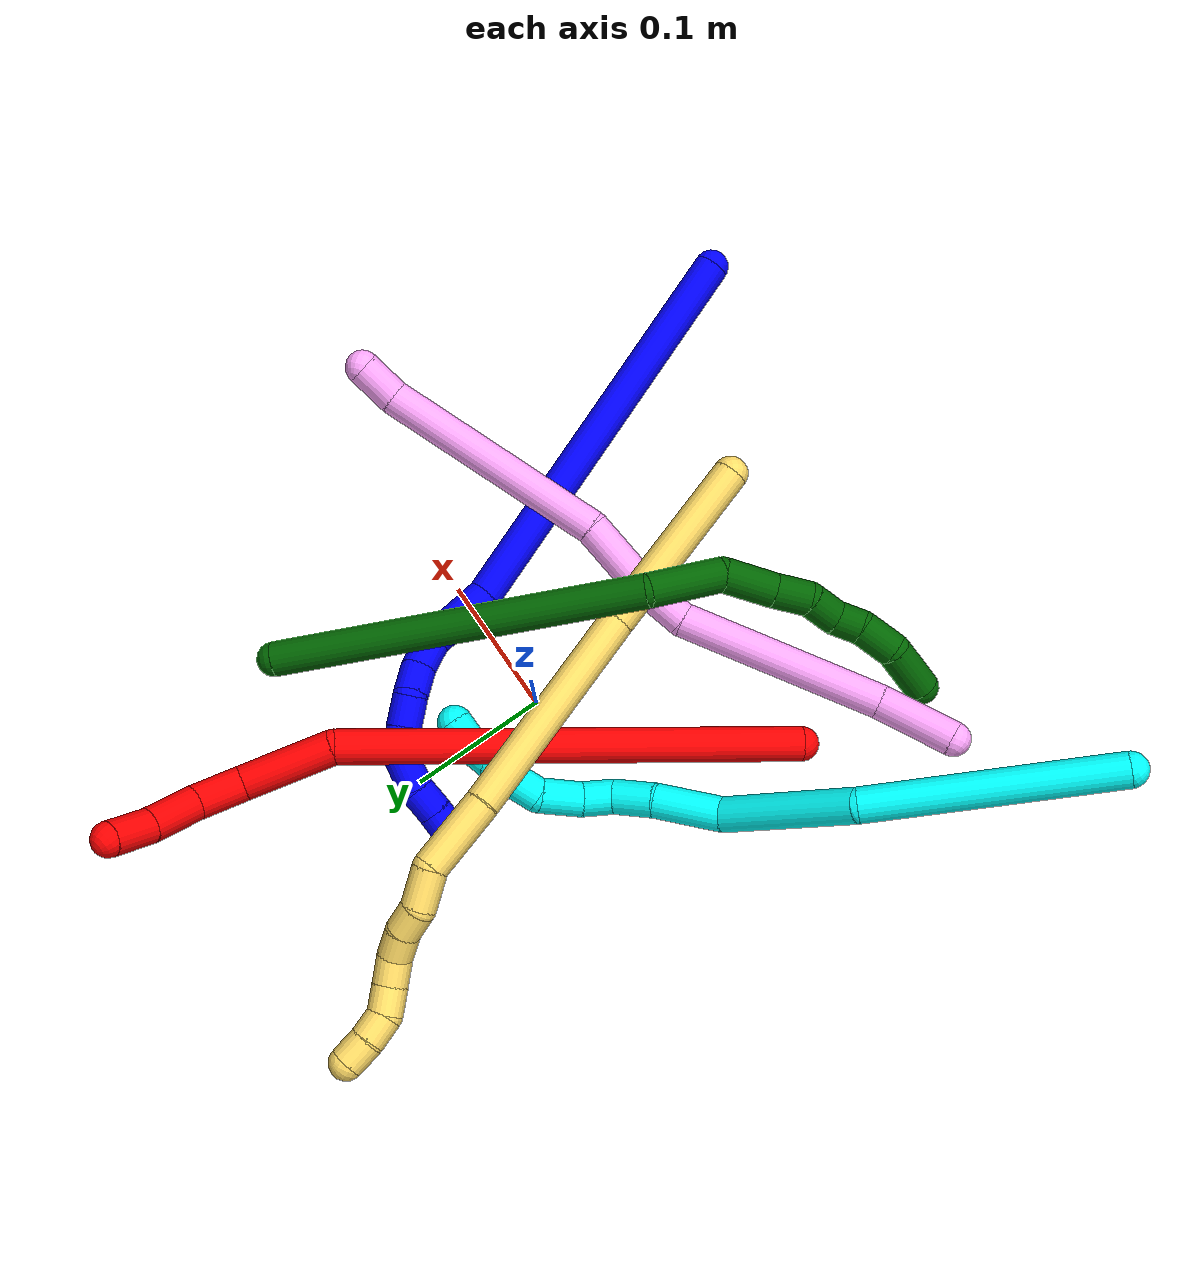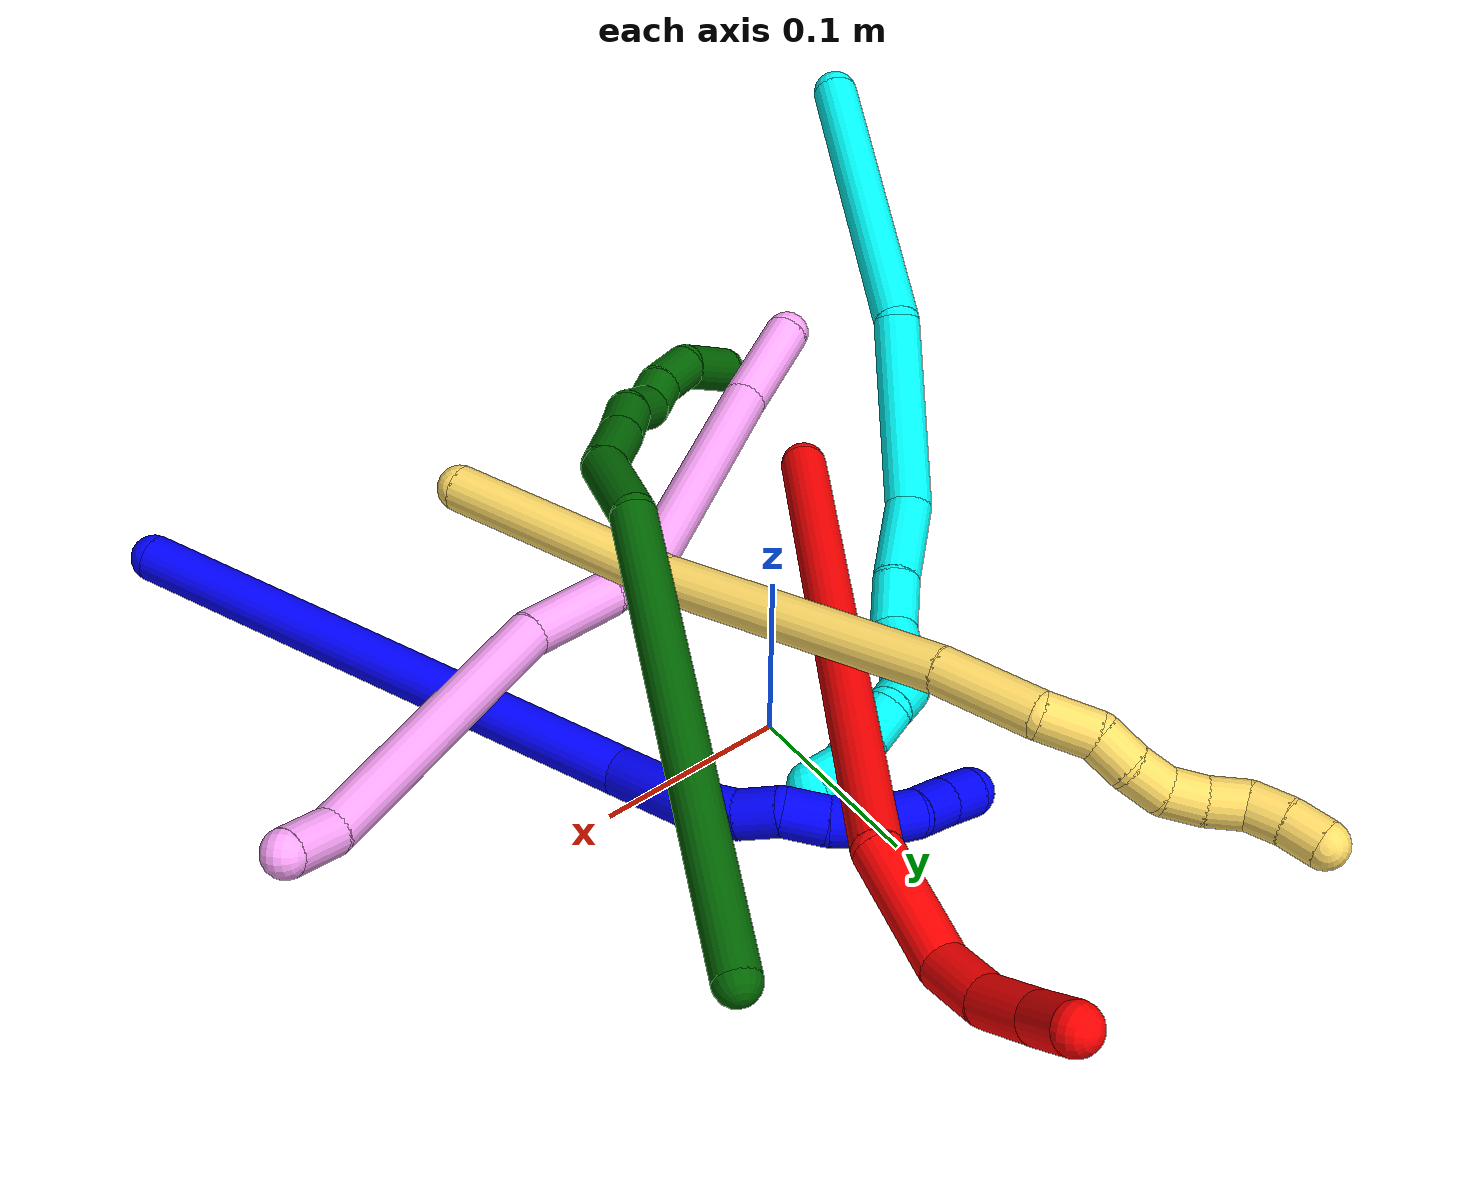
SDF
<sdf version="1.7">
 <world name="default">
  <plugin name="TubeGeneratorPlugin" filename="libtube_generator_plugin.so"/>
  <model name="photoneo_s_sensor">
   <static>1</static>
   <pose>0 0 2 1.57079 1.57079 3.14159</pose>
   <link name="link">
    <inertial><mass>0.1</mass></inertial>
    <sensor name="sensor" type="depth">
     <update_rate>30</update_rate>
     <camera>
      <horizontal_fov>1.22</horizontal_fov>
      <image><width>1920</width><height>1200</height><format>B8G8R8</format></image>
      <clip><near>0.1</near><far>4</far></clip>
      <depth_camera><output>points</output></depth_camera>
     </camera>
     <plugin name="camera_plugin" filename="libgazebo_ros_depth_camera.so">
      <baseline>0.2</baseline>
      <alwaysOn>1</alwaysOn>
      <updateRate>0.0</updateRate>
      <cameraName>camera_ir</cameraName>
      <imageTopicName>/camera/color/image_raw</imageTopicName>
      <cameraInfoTopicName>/camera/color/camera_info</cameraInfoTopicName>
      <depthImageTopicName>/camera/depth/image_raw</depthImageTopicName>
      <depthImageCameraInfoTopicName>/camera/depth/camera_info</depthImageCameraInfoTopicName>
      <pointCloudTopicName>/camera/depth/points</pointCloudTopicName>
      <frameName>fr_optical</frameName>
      <pointCloudCutoff>0.1</pointCloudCutoff>
      <pointCloudCutoffMax>2.0</pointCloudCutoffMax>
      <distortionK1>0</distortionK1>
      <distortionK2>0</distortionK2>
      <distortionK3>0</distortionK3>
      <distortionT1>0</distortionT1>
      <distortionT2>0</distortionT2>
      <CxPrime>0</CxPrime>
      <Cx>0</Cx>
      <Cy>0</Cy>
      <focalLength>0</focalLength>
      <hackBaseline>0</hackBaseline>
     </plugin>
    </sensor>
   </link>
  </model>
  <gravity>0 0 -9.8</gravity>
  <magnetic_field>6e-06 2.3e-05 -4.2e-05</magnetic_field>
  <atmosphere type="adiabatic"/>
  <physics name="default_physics" default="0" type="ode">
   <max_step_size>0.003</max_step_size>
   <real_time_factor>1</real_time_factor>
   <real_time_update_rate>1000</real_time_update_rate>
   <max_contacts>10000</max_contacts>
   <ode>
    <solver>
     <type>quick</type>
     <iters>100</iters>
     <sor>1.3</sor>
     <use_dynamic_moi_rescaling>0</use_dynamic_moi_rescaling>
    </solver>
    <constraints>
     <contact_max_correcting_vel>0</contact_max_correcting_vel>
     <contact_surface_layer>0.001</contact_surface_layer>
     <cfm>0</cfm>
     <erp>0.2</erp>
    </constraints>
   </ode>
  </physics>
  <scene><ambient>0.4 0.4 0.4 1</ambient><background>0.7 0.7 0.7 1</background><shadows>0</shadows></scene>
  <audio><device>default</device></audio>
  <spherical_coordinates>
   <surface_model>EARTH_WGS84</surface_model>
   <latitude_deg>0</latitude_deg>
   <longitude_deg>0</longitude_deg>
   <elevation>0</elevation>
   <heading_deg>0</heading_deg>
  </spherical_coordinates>
  <model name="bin">
   <static>1</static>
   <link name="bottom">
    <collision name="collision-bottom">
     <pose>0 0 -0.01 0 -0 0</pose>
     <geometry><box><size>0.8 0.6 0.02</size></box></geometry>
     <surface>
      <friction><ode><mu>100</mu><mu2>100</mu2></ode></friction>
      <contact><collide_bitmask>65535</collide_bitmask></contact>
     </surface>
    </collision>
   </link>
   <link name="west_wall">
    <collision name="collision-west_wall">
     <pose>-0.41 0 0.1 0 -0 0</pose>
     <geometry><box><size>0.02 0.6 0.2</size></box></geometry>
     <surface>
      <friction><ode><mu>100</mu><mu2>100</mu2></ode></friction>
      <contact><collide_bitmask>65535</collide_bitmask></contact>
     </surface>
    </collision>
   </link>
   <link name="east_wall">
    <collision name="collision-east_wall">
     <pose>0.41 0 0.1 0 -0 0</pose>
     <geometry><box><size>0.02 0.6 0.2</size></box></geometry>
     <surface>
      <friction><ode><mu>100</mu><mu2>100</mu2></ode></friction>
      <contact><collide_bitmask>65535</collide_bitmask></contact>
     </surface>
    </collision>
   </link>
   <link name="south_wall">
    <collision name="collision-south_wall">
     <pose>0 -0.31 0.1 0 -0 0</pose>
     <geometry><box><size>0.8 0.02 0.2</size></box></geometry>
     <surface>
      <friction><ode><mu>100</mu><mu2>100</mu2></ode></friction>
      <contact><collide_bitmask>65535</collide_bitmask></contact>
     </surface>
    </collision>
   </link>
   <link name="north_wall">
    <collision name="collision-north_wall">
     <pose>0 0.31 0.1 0 -0 0</pose>
     <geometry><box><size>0.8 0.02 0.2</size></box></geometry>
     <surface>
      <friction><ode><mu>100</mu><mu2>100</mu2></ode></friction>
      <contact><collide_bitmask>65535</collide_bitmask></contact>
     </surface>
    </collision>
   </link>
  </model>
  <model name="1">
   <static>0</static>
   <link name="1">
    <collision name="collision-cylinder-e_1_1_4">
     <pose>-0.062034 0.10084 -0.087991 -2.28825 -0.434039 0.903197</pose>
     <geometry><cylinder><radius>0.0125</radius><length>0.29502</length></cylinder></geometry>
     <surface>
      <friction><ode><mu>1.16</mu><mu2>1.16</mu2><slip1>0</slip1><slip2>0</slip2></ode></friction>
      <contact><ode><kp>1e+06</kp><kd>1</kd><max_vel>0</max_vel><min_depth>0.001</min_depth></ode></contact>
     </surface>
    </collision>
    <visual name="visual-cylinder-e_1_1_4">
     <pose>-0.062034 0.10084 -0.087991 -2.28825 -0.434039 0.903197</pose>
     <geometry><cylinder><radius>0.0125</radius><length>0.29502</length></cylinder></geometry>
     <material><ambient>0 0 1 1</ambient></material>
    </visual>
    <collision name="collision-cylinder-e_2_4_5">
     <pose>-0.128251 0.223685 -0.189242 -2.11314 -0.161436 0.284455</pose>
     <geometry><cylinder><radius>0.0125</radius><length>0.052062</length></cylinder></geometry>
     <surface>
      <friction><ode><mu>1.16</mu><mu2>1.16</mu2><slip1>0</slip1><slip2>0</slip2></ode></friction>
      <contact><ode><kp>1e+06</kp><kd>1</kd><max_vel>0</max_vel><min_depth>0.001</min_depth></ode></contact>
     </surface>
    </collision>
    <visual name="visual-cylinder-e_2_4_5">
     <pose>-0.128251 0.223685 -0.189242 -2.11314 -0.161436 0.284455</pose>
     <geometry><cylinder><radius>0.0125</radius><length>0.052062</length></cylinder></geometry>
     <material><ambient>0 0 1 1</ambient></material>
    </visual>
    <collision name="collision-cylinder-e_3_5_6">
     <pose>-0.137871 0.254146 -0.207088 -2.06768 -0.514343 0.832002</pose>
     <geometry><cylinder><radius>0.0125</radius><length>0.022096</length></cylinder></geometry>
     <surface>
      <friction><ode><mu>1.16</mu><mu2>1.16</mu2><slip1>0</slip1><slip2>0</slip2></ode></friction>
      <contact><ode><kp>1e+06</kp><kd>1</kd><max_vel>0</max_vel><min_depth>0.001</min_depth></ode></contact>
     </surface>
    </collision>
    <visual name="visual-cylinder-e_3_5_6">
     <pose>-0.137871 0.254146 -0.207088 -2.06768 -0.514343 0.832002</pose>
     <geometry><cylinder><radius>0.0125</radius><length>0.022096</length></cylinder></geometry>
     <material><ambient>0 0 1 1</ambient></material>
    </visual>
    <collision name="collision-cylinder-e_4_6_7">
     <pose>-0.149668 0.271443 -0.213567 -1.78176 -0.61316 0.746365</pose>
     <geometry><cylinder><radius>0.0125</radius><length>0.022111</length></cylinder></geometry>
     <surface>
      <friction><ode><mu>1.16</mu><mu2>1.16</mu2><slip1>0</slip1><slip2>0</slip2></ode></friction>
      <contact><ode><kp>1e+06</kp><kd>1</kd><max_vel>0</max_vel><min_depth>0.001</min_depth></ode></contact>
     </surface>
    </collision>
    <visual name="visual-cylinder-e_4_6_7">
     <pose>-0.149668 0.271443 -0.213567 -1.78176 -0.61316 0.746365</pose>
     <geometry><cylinder><radius>0.0125</radius><length>0.022111</length></cylinder></geometry>
     <material><ambient>0 0 1 1</ambient></material>
    </visual>
    <collision name="collision-cylinder-e_5_7_8">
     <pose>-0.164446 0.286082 -0.220418 -2.27823 -0.834491 1.53234</pose>
     <geometry><cylinder><radius>0.0125</radius><length>0.022718</length></cylinder></geometry>
     <surface>
      <friction><ode><mu>1.16</mu><mu2>1.16</mu2><slip1>0</slip1><slip2>0</slip2></ode></friction>
      <contact><ode><kp>1e+06</kp><kd>1</kd><max_vel>0</max_vel><min_depth>0.001</min_depth></ode></contact>
     </surface>
    </collision>
    <visual name="visual-cylinder-e_5_7_8">
     <pose>-0.164446 0.286082 -0.220418 -2.27823 -0.834491 1.53234</pose>
     <geometry><cylinder><radius>0.0125</radius><length>0.022718</length></cylinder></geometry>
     <material><ambient>0 0 1 1</ambient></material>
    </visual>
    <collision name="collision-cylinder-e_6_8_9">
     <pose>-0.181272 0.297478 -0.22816 -2.0324 -0.931406 1.36321</pose>
     <geometry><cylinder><radius>0.0125</radius><length>0.020958</length></cylinder></geometry>
     <surface>
      <friction><ode><mu>1.16</mu><mu2>1.16</mu2><slip1>0</slip1><slip2>0</slip2></ode></friction>
      <contact><ode><kp>1e+06</kp><kd>1</kd><max_vel>0</max_vel><min_depth>0.001</min_depth></ode></contact>
     </surface>
    </collision>
    <visual name="visual-cylinder-e_6_8_9">
     <pose>-0.181272 0.297478 -0.22816 -2.0324 -0.931406 1.36321</pose>
     <geometry><cylinder><radius>0.0125</radius><length>0.020958</length></cylinder></geometry>
     <material><ambient>0 0 1 1</ambient></material>
    </visual>
    <collision name="collision-cylinder-e_7_9_10">
     <pose>-0.20172 0.304556 -0.231266 -1.78444 -1.44572 1.66056</pose>
     <geometry><cylinder><radius>0.0125</radius><length>0.024268</length></cylinder></geometry>
     <surface>
      <friction><ode><mu>1.16</mu><mu2>1.16</mu2><slip1>0</slip1><slip2>0</slip2></ode></friction>
      <contact><ode><kp>1e+06</kp><kd>1</kd><max_vel>0</max_vel><min_depth>0.001</min_depth></ode></contact>
     </surface>
    </collision>
    <visual name="visual-cylinder-e_7_9_10">
     <pose>-0.20172 0.304556 -0.231266 -1.78444 -1.44572 1.66056</pose>
     <geometry><cylinder><radius>0.0125</radius><length>0.024268</length></cylinder></geometry>
     <material><ambient>0 0 1 1</ambient></material>
    </visual>
    <collision name="collision-cylinder-e_8_10_11">
     <pose>-0.223908 0.304735 -0.230359 0.81383 -1.39643 -0.694099</pose>
     <geometry><cylinder><radius>0.0125</radius><length>0.020611</length></cylinder></geometry>
     <surface>
      <friction><ode><mu>1.16</mu><mu2>1.16</mu2><slip1>0</slip1><slip2>0</slip2></ode></friction>
      <contact><ode><kp>1e+06</kp><kd>1</kd><max_vel>0</max_vel><min_depth>0.001</min_depth></ode></contact>
     </surface>
    </collision>
    <visual name="visual-cylinder-e_8_10_11">
     <pose>-0.223908 0.304735 -0.230359 0.81383 -1.39643 -0.694099</pose>
     <geometry><cylinder><radius>0.0125</radius><length>0.020611</length></cylinder></geometry>
     <material><ambient>0 0 1 1</ambient></material>
    </visual>
    <collision name="collision-cylinder-e_9_11_2">
     <pose>-0.244073 0.302737 -0.228258 0.674574 -1.45956 -0.607952</pose>
     <geometry><cylinder><radius>0.0125</radius><length>0.020156</length></cylinder></geometry>
     <surface>
      <friction><ode><mu>1.16</mu><mu2>1.16</mu2><slip1>0</slip1><slip2>0</slip2></ode></friction>
      <contact><ode><kp>1e+06</kp><kd>1</kd><max_vel>0</max_vel><min_depth>0.001</min_depth></ode></contact>
     </surface>
    </collision>
    <visual name="visual-cylinder-e_9_11_2">
     <pose>-0.244073 0.302737 -0.228258 0.674574 -1.45956 -0.607952</pose>
     <geometry><cylinder><radius>0.0125</radius><length>0.020156</length></cylinder></geometry>
     <material><ambient>0 0 1 1</ambient></material>
    </visual>
    <collision name="collision-sphere-2">
     <pose>-0.254089 0.302038 -0.227384 0 -0 0</pose>
     <geometry><sphere><radius>0.0125</radius></sphere></geometry>
     <surface>
      <friction><ode><mu>1.16</mu><mu2>1.16</mu2><slip1>0</slip1><slip2>0</slip2></ode></friction>
      <contact><ode><kp>1e+06</kp><kd>1</kd><max_vel>0</max_vel><min_depth>0.001</min_depth></ode></contact>
     </surface>
    </collision>
    <visual name="visual-sphere-2">
     <pose>-0.254089 0.302038 -0.227384 0 -0 0</pose>
     <geometry><sphere><radius>0.0125</radius></sphere></geometry>
     <material><ambient>0 0 1 1</ambient></material>
    </visual>
    <collision name="collision-sphere-11">
     <pose>-0.234058 0.303436 -0.229131 0 -0 0</pose>
     <geometry><sphere><radius>0.0125</radius></sphere></geometry>
     <surface>
      <friction><ode><mu>1.16</mu><mu2>1.16</mu2><slip1>0</slip1><slip2>0</slip2></ode></friction>
      <contact><ode><kp>1e+06</kp><kd>1</kd><max_vel>0</max_vel><min_depth>0.001</min_depth></ode></contact>
     </surface>
    </collision>
    <visual name="visual-sphere-11">
     <pose>-0.234058 0.303436 -0.229131 0 -0 0</pose>
     <geometry><sphere><radius>0.0125</radius></sphere></geometry>
     <material><ambient>0 0 1 1</ambient></material>
    </visual>
    <collision name="collision-sphere-10">
     <pose>-0.213759 0.306035 -0.231587 0 -0 0</pose>
     <geometry><sphere><radius>0.0125</radius></sphere></geometry>
     <surface>
      <friction><ode><mu>1.16</mu><mu2>1.16</mu2><slip1>0</slip1><slip2>0</slip2></ode></friction>
      <contact><ode><kp>1e+06</kp><kd>1</kd><max_vel>0</max_vel><min_depth>0.001</min_depth></ode></contact>
     </surface>
    </collision>
    <visual name="visual-sphere-10">
     <pose>-0.213759 0.306035 -0.231587 0 -0 0</pose>
     <geometry><sphere><radius>0.0125</radius></sphere></geometry>
     <material><ambient>0 0 1 1</ambient></material>
    </visual>
    <collision name="collision-sphere-9">
     <pose>-0.189681 0.303076 -0.230945 0 -0 0</pose>
     <geometry><sphere><radius>0.0125</radius></sphere></geometry>
     <surface>
      <friction><ode><mu>1.16</mu><mu2>1.16</mu2><slip1>0</slip1><slip2>0</slip2></ode></friction>
      <contact><ode><kp>1e+06</kp><kd>1</kd><max_vel>0</max_vel><min_depth>0.001</min_depth></ode></contact>
     </surface>
    </collision>
    <visual name="visual-sphere-9">
     <pose>-0.189681 0.303076 -0.230945 0 -0 0</pose>
     <geometry><sphere><radius>0.0125</radius></sphere></geometry>
     <material><ambient>0 0 1 1</ambient></material>
    </visual>
    <collision name="collision-sphere-4">
     <pose>-0.124067 0.201679 -0.175981 0 -0 0</pose>
     <geometry><sphere><radius>0.0125</radius></sphere></geometry>
     <surface>
      <friction><ode><mu>1.16</mu><mu2>1.16</mu2><slip1>0</slip1><slip2>0</slip2></ode></friction>
      <contact><ode><kp>1e+06</kp><kd>1</kd><max_vel>0</max_vel><min_depth>0.001</min_depth></ode></contact>
     </surface>
    </collision>
    <visual name="visual-sphere-4">
     <pose>-0.124067 0.201679 -0.175981 0 -0 0</pose>
     <geometry><sphere><radius>0.0125</radius></sphere></geometry>
     <material><ambient>0 0 1 1</ambient></material>
    </visual>
    <collision name="collision-sphere-1">
     <geometry><sphere><radius>0.0125</radius></sphere></geometry>
     <surface>
      <friction><ode><mu>1.16</mu><mu2>1.16</mu2><slip1>0</slip1><slip2>0</slip2></ode></friction>
      <contact><ode><kp>1e+06</kp><kd>1</kd><max_vel>0</max_vel><min_depth>0.001</min_depth></ode></contact>
     </surface>
    </collision>
    <visual name="visual-sphere-1">
     <geometry><sphere><radius>0.0125</radius></sphere></geometry>
     <material><ambient>0 0 1 1</ambient></material>
    </visual>
    <collision name="collision-sphere-8">
     <pose>-0.172863 0.291879 -0.225375 0 -0 0</pose>
     <geometry><sphere><radius>0.0125</radius></sphere></geometry>
     <surface>
      <friction><ode><mu>1.16</mu><mu2>1.16</mu2><slip1>0</slip1><slip2>0</slip2></ode></friction>
      <contact><ode><kp>1e+06</kp><kd>1</kd><max_vel>0</max_vel><min_depth>0.001</min_depth></ode></contact>
     </surface>
    </collision>
    <visual name="visual-sphere-8">
     <pose>-0.172863 0.291879 -0.225375 0 -0 0</pose>
     <geometry><sphere><radius>0.0125</radius></sphere></geometry>
     <material><ambient>0 0 1 1</ambient></material>
    </visual>
    <collision name="collision-sphere-5">
     <pose>-0.132435 0.245691 -0.202503 0 -0 0</pose>
     <geometry><sphere><radius>0.0125</radius></sphere></geometry>
     <surface>
      <friction><ode><mu>1.16</mu><mu2>1.16</mu2><slip1>0</slip1><slip2>0</slip2></ode></friction>
      <contact><ode><kp>1e+06</kp><kd>1</kd><max_vel>0</max_vel><min_depth>0.001</min_depth></ode></contact>
     </surface>
    </collision>
    <visual name="visual-sphere-5">
     <pose>-0.132435 0.245691 -0.202503 0 -0 0</pose>
     <geometry><sphere><radius>0.0125</radius></sphere></geometry>
     <material><ambient>0 0 1 1</ambient></material>
    </visual>
    <collision name="collision-sphere-6">
     <pose>-0.143306 0.262601 -0.211673 0 -0 0</pose>
     <geometry><sphere><radius>0.0125</radius></sphere></geometry>
     <surface>
      <friction><ode><mu>1.16</mu><mu2>1.16</mu2><slip1>0</slip1><slip2>0</slip2></ode></friction>
      <contact><ode><kp>1e+06</kp><kd>1</kd><max_vel>0</max_vel><min_depth>0.001</min_depth></ode></contact>
     </surface>
    </collision>
    <visual name="visual-sphere-6">
     <pose>-0.143306 0.262601 -0.211673 0 -0 0</pose>
     <geometry><sphere><radius>0.0125</radius></sphere></geometry>
     <material><ambient>0 0 1 1</ambient></material>
    </visual>
    <collision name="collision-sphere-7">
     <pose>-0.15603 0.280284 -0.21546 0 -0 0</pose>
     <geometry><sphere><radius>0.0125</radius></sphere></geometry>
     <surface>
      <friction><ode><mu>1.16</mu><mu2>1.16</mu2><slip1>0</slip1><slip2>0</slip2></ode></friction>
      <contact><ode><kp>1e+06</kp><kd>1</kd><max_vel>0</max_vel><min_depth>0.001</min_depth></ode></contact>
     </surface>
    </collision>
    <visual name="visual-sphere-7">
     <pose>-0.15603 0.280284 -0.21546 0 -0 0</pose>
     <geometry><sphere><radius>0.0125</radius></sphere></geometry>
     <material><ambient>0 0 1 1</ambient></material>
    </visual>
    <inertial>
     <pose>-0.106597 0.171041 -0.139719 0 -0 0</pose>
     <mass>0.5</mass>
     <inertia>
      <ixx>0.002745</ixx>
      <ixy>0</ixy>
      <ixz>0</ixz>
      <iyy>0.001225</iyy>
      <iyz>0</iyz>
      <izz>-0.000588</izz>
     </inertia>
    </inertial>
   </link>
   <pose>0.192632 -0.286871 0.013241 0.864251 -0.319114 -0.080401</pose>
  </model>
  <model name="2">
   <static>0</static>
   <link name="2">
    <collision name="collision-cylinder-e_1_1_4">
     <pose>0.087086 0.072429 0.118506 -0.548604 0.560055 -0.161498</pose>
     <geometry><cylinder><radius>0.0125</radius><length>0.327862</length></cylinder></geometry>
     <surface>
      <friction><ode><mu>1.16</mu><mu2>1.16</mu2><slip1>0</slip1><slip2>0</slip2></ode></friction>
      <contact><ode><kp>1e+06</kp><kd>1</kd><max_vel>0</max_vel><min_depth>0.001</min_depth></ode></contact>
     </surface>
    </collision>
    <visual name="visual-cylinder-e_1_1_4">
     <pose>0.087086 0.072429 0.118506 -0.548604 0.560055 -0.161498</pose>
     <geometry><cylinder><radius>0.0125</radius><length>0.327862</length></cylinder></geometry>
     <material><ambient>1 0 0 1</ambient></material>
    </visual>
    <collision name="collision-cylinder-e_2_4_5">
     <pose>0.178755 0.164386 0.264074 -0.625047 0.136496 -0.044165</pose>
     <geometry><cylinder><radius>0.0125</radius><length>0.067372</length></cylinder></geometry>
     <surface>
      <friction><ode><mu>1.16</mu><mu2>1.16</mu2><slip1>0</slip1><slip2>0</slip2></ode></friction>
      <contact><ode><kp>1e+06</kp><kd>1</kd><max_vel>0</max_vel><min_depth>0.001</min_depth></ode></contact>
     </surface>
    </collision>
    <visual name="visual-cylinder-e_2_4_5">
     <pose>0.178755 0.164386 0.264074 -0.625047 0.136496 -0.044165</pose>
     <geometry><cylinder><radius>0.0125</radius><length>0.067372</length></cylinder></geometry>
     <material><ambient>1 0 0 1</ambient></material>
    </visual>
    <collision name="collision-cylinder-e_3_5_6">
     <pose>0.187955 0.186679 0.308167 -0.161032 0.261466 -0.021218</pose>
     <geometry><cylinder><radius>0.0125</radius><length>0.035718</length></cylinder></geometry>
     <surface>
      <friction><ode><mu>1.16</mu><mu2>1.16</mu2><slip1>0</slip1><slip2>0</slip2></ode></friction>
      <contact><ode><kp>1e+06</kp><kd>1</kd><max_vel>0</max_vel><min_depth>0.001</min_depth></ode></contact>
     </surface>
    </collision>
    <visual name="visual-cylinder-e_3_5_6">
     <pose>0.187955 0.186679 0.308167 -0.161032 0.261466 -0.021218</pose>
     <geometry><cylinder><radius>0.0125</radius><length>0.035718</length></cylinder></geometry>
     <material><ambient>1 0 0 1</ambient></material>
    </visual>
    <collision name="collision-cylinder-e_4_6_7">
     <pose>0.196999 0.187576 0.343319 0.102787 0.238356 0.012319</pose>
     <geometry><cylinder><radius>0.0125</radius><length>0.0375</length></cylinder></geometry>
     <surface>
      <friction><ode><mu>1.16</mu><mu2>1.16</mu2><slip1>0</slip1><slip2>0</slip2></ode></friction>
      <contact><ode><kp>1e+06</kp><kd>1</kd><max_vel>0</max_vel><min_depth>0.001</min_depth></ode></contact>
     </surface>
    </collision>
    <visual name="visual-cylinder-e_4_6_7">
     <pose>0.196999 0.187576 0.343319 0.102787 0.238356 0.012319</pose>
     <geometry><cylinder><radius>0.0125</radius><length>0.0375</length></cylinder></geometry>
     <material><ambient>1 0 0 1</ambient></material>
    </visual>
    <collision name="collision-cylinder-e_5_7_2">
     <pose>0.20734 0.182994 0.375812 0.186572 0.384341 0.036403</pose>
     <geometry><cylinder><radius>0.0125</radius><length>0.031548</length></cylinder></geometry>
     <surface>
      <friction><ode><mu>1.16</mu><mu2>1.16</mu2><slip1>0</slip1><slip2>0</slip2></ode></friction>
      <contact><ode><kp>1e+06</kp><kd>1</kd><max_vel>0</max_vel><min_depth>0.001</min_depth></ode></contact>
     </surface>
    </collision>
    <visual name="visual-cylinder-e_5_7_2">
     <pose>0.20734 0.182994 0.375812 0.186572 0.384341 0.036403</pose>
     <geometry><cylinder><radius>0.0125</radius><length>0.031548</length></cylinder></geometry>
     <material><ambient>1 0 0 1</ambient></material>
    </visual>
    <collision name="collision-sphere-2">
     <pose>0.213254 0.180282 0.390181 0 -0 0</pose>
     <geometry><sphere><radius>0.0125</radius></sphere></geometry>
     <surface>
      <friction><ode><mu>1.16</mu><mu2>1.16</mu2><slip1>0</slip1><slip2>0</slip2></ode></friction>
      <contact><ode><kp>1e+06</kp><kd>1</kd><max_vel>0</max_vel><min_depth>0.001</min_depth></ode></contact>
     </surface>
    </collision>
    <visual name="visual-sphere-2">
     <pose>0.213254 0.180282 0.390181 0 -0 0</pose>
     <geometry><sphere><radius>0.0125</radius></sphere></geometry>
     <material><ambient>1 0 0 1</ambient></material>
    </visual>
    <collision name="collision-sphere-7">
     <pose>0.201426 0.185707 0.361443 0 -0 0</pose>
     <geometry><sphere><radius>0.0125</radius></sphere></geometry>
     <surface>
      <friction><ode><mu>1.16</mu><mu2>1.16</mu2><slip1>0</slip1><slip2>0</slip2></ode></friction>
      <contact><ode><kp>1e+06</kp><kd>1</kd><max_vel>0</max_vel><min_depth>0.001</min_depth></ode></contact>
     </surface>
    </collision>
    <visual name="visual-sphere-7">
     <pose>0.201426 0.185707 0.361443 0 -0 0</pose>
     <geometry><sphere><radius>0.0125</radius></sphere></geometry>
     <material><ambient>1 0 0 1</ambient></material>
    </visual>
    <collision name="collision-sphere-6">
     <pose>0.192572 0.189446 0.325195 0 -0 0</pose>
     <geometry><sphere><radius>0.0125</radius></sphere></geometry>
     <surface>
      <friction><ode><mu>1.16</mu><mu2>1.16</mu2><slip1>0</slip1><slip2>0</slip2></ode></friction>
      <contact><ode><kp>1e+06</kp><kd>1</kd><max_vel>0</max_vel><min_depth>0.001</min_depth></ode></contact>
     </surface>
    </collision>
    <visual name="visual-sphere-6">
     <pose>0.192572 0.189446 0.325195 0 -0 0</pose>
     <geometry><sphere><radius>0.0125</radius></sphere></geometry>
     <material><ambient>1 0 0 1</ambient></material>
    </visual>
    <collision name="collision-sphere-5">
     <pose>0.183339 0.183913 0.291138 0 -0 0</pose>
     <geometry><sphere><radius>0.0125</radius></sphere></geometry>
     <surface>
      <friction><ode><mu>1.16</mu><mu2>1.16</mu2><slip1>0</slip1><slip2>0</slip2></ode></friction>
      <contact><ode><kp>1e+06</kp><kd>1</kd><max_vel>0</max_vel><min_depth>0.001</min_depth></ode></contact>
     </surface>
    </collision>
    <visual name="visual-sphere-5">
     <pose>0.183339 0.183913 0.291138 0 -0 0</pose>
     <geometry><sphere><radius>0.0125</radius></sphere></geometry>
     <material><ambient>1 0 0 1</ambient></material>
    </visual>
    <collision name="collision-sphere-1">
     <geometry><sphere><radius>0.0125</radius></sphere></geometry>
     <surface>
      <friction><ode><mu>1.16</mu><mu2>1.16</mu2><slip1>0</slip1><slip2>0</slip2></ode></friction>
      <contact><ode><kp>1e+06</kp><kd>1</kd><max_vel>0</max_vel><min_depth>0.001</min_depth></ode></contact>
     </surface>
    </collision>
    <visual name="visual-sphere-1">
     <geometry><sphere><radius>0.0125</radius></sphere></geometry>
     <material><ambient>1 0 0 1</ambient></material>
    </visual>
    <collision name="collision-sphere-4">
     <pose>0.174171 0.144858 0.237011 0 -0 0</pose>
     <geometry><sphere><radius>0.0125</radius></sphere></geometry>
     <surface>
      <friction><ode><mu>1.16</mu><mu2>1.16</mu2><slip1>0</slip1><slip2>0</slip2></ode></friction>
      <contact><ode><kp>1e+06</kp><kd>1</kd><max_vel>0</max_vel><min_depth>0.001</min_depth></ode></contact>
     </surface>
    </collision>
    <visual name="visual-sphere-4">
     <pose>0.174171 0.144858 0.237011 0 -0 0</pose>
     <geometry><sphere><radius>0.0125</radius></sphere></geometry>
     <material><ambient>1 0 0 1</ambient></material>
    </visual>
    <inertial>
     <pose>0.122474 0.108593 0.184764 0 -0 0</pose>
     <mass>0.5</mass>
     <inertia>
      <ixx>0.002122</ixx>
      <ixy>0</ixy>
      <ixz>0</ixz>
      <iyy>0.002264</iyy>
      <iyz>0</iyz>
      <izz>-0.002864</izz>
     </inertia>
    </inertial>
   </link>
   <pose>-0.131992 -0.136514 0.011703 -1.13619 -0.463914 -0.026741</pose>
  </model>
  <model name="3">
   <static>0</static>
   <link name="3">
    <collision name="collision-cylinder-e_1_1_4">
     <pose>0.003632 0.031284 -0.084087 -2.78542 0.040457 -0.22386</pose>
     <geometry><cylinder><radius>0.0125</radius><length>0.179582</length></cylinder></geometry>
     <surface>
      <friction><ode><mu>1.16</mu><mu2>1.16</mu2><slip1>0</slip1><slip2>0</slip2></ode></friction>
      <contact><ode><kp>1e+06</kp><kd>1</kd><max_vel>0</max_vel><min_depth>0.001</min_depth></ode></contact>
     </surface>
    </collision>
    <visual name="visual-cylinder-e_1_1_4">
     <pose>0.003632 0.031284 -0.084087 -2.78542 0.040457 -0.22386</pose>
     <geometry><cylinder><radius>0.0125</radius><length>0.179582</length></cylinder></geometry>
     <material><ambient>0.003922 1 0.996078 1</ambient></material>
    </visual>
    <collision name="collision-cylinder-e_2_4_5">
     <pose>0.017989 0.060933 -0.21939 3.10969 0.206321 2.83582</pose>
     <geometry><cylinder><radius>0.0125</radius><length>0.104707</length></cylinder></geometry>
     <surface>
      <friction><ode><mu>1.16</mu><mu2>1.16</mu2><slip1>0</slip1><slip2>0</slip2></ode></friction>
      <contact><ode><kp>1e+06</kp><kd>1</kd><max_vel>0</max_vel><min_depth>0.001</min_depth></ode></contact>
     </surface>
    </collision>
    <visual name="visual-cylinder-e_2_4_5">
     <pose>0.017989 0.060933 -0.21939 3.10969 0.206321 2.83582</pose>
     <geometry><cylinder><radius>0.0125</radius><length>0.104707</length></cylinder></geometry>
     <material><ambient>0.003922 1 0.996078 1</ambient></material>
    </visual>
    <collision name="collision-cylinder-e_3_5_6">
     <pose>0.037507 0.068718 -0.291455 -2.7172 0.36695 -1.42205</pose>
     <geometry><cylinder><radius>0.0125</radius><length>0.049017</length></cylinder></geometry>
     <surface>
      <friction><ode><mu>1.16</mu><mu2>1.16</mu2><slip1>0</slip1><slip2>0</slip2></ode></friction>
      <contact><ode><kp>1e+06</kp><kd>1</kd><max_vel>0</max_vel><min_depth>0.001</min_depth></ode></contact>
     </surface>
    </collision>
    <visual name="visual-cylinder-e_3_5_6">
     <pose>0.037507 0.068718 -0.291455 -2.7172 0.36695 -1.42205</pose>
     <geometry><cylinder><radius>0.0125</radius><length>0.049017</length></cylinder></geometry>
     <material><ambient>0.003922 1 0.996078 1</ambient></material>
    </visual>
    <collision name="collision-cylinder-e_4_6_7">
     <pose>0.050759 0.081877 -0.326404 -2.88243 0.296638 -1.70717</pose>
     <geometry><cylinder><radius>0.0125</radius><length>0.030511</length></cylinder></geometry>
     <surface>
      <friction><ode><mu>1.16</mu><mu2>1.16</mu2><slip1>0</slip1><slip2>0</slip2></ode></friction>
      <contact><ode><kp>1e+06</kp><kd>1</kd><max_vel>0</max_vel><min_depth>0.001</min_depth></ode></contact>
     </surface>
    </collision>
    <visual name="visual-cylinder-e_4_6_7">
     <pose>0.050759 0.081877 -0.326404 -2.88243 0.296638 -1.70717</pose>
     <geometry><cylinder><radius>0.0125</radius><length>0.030511</length></cylinder></geometry>
     <material><ambient>0.003922 1 0.996078 1</ambient></material>
    </visual>
    <collision name="collision-cylinder-e_5_7_8">
     <pose>0.05559 0.091488 -0.350363 -2.60433 0.032399 -0.117566</pose>
     <geometry><cylinder><radius>0.0125</radius><length>0.022959</length></cylinder></geometry>
     <surface>
      <friction><ode><mu>1.16</mu><mu2>1.16</mu2><slip1>0</slip1><slip2>0</slip2></ode></friction>
      <contact><ode><kp>1e+06</kp><kd>1</kd><max_vel>0</max_vel><min_depth>0.001</min_depth></ode></contact>
     </surface>
    </collision>
    <visual name="visual-cylinder-e_5_7_8">
     <pose>0.05559 0.091488 -0.350363 -2.60433 0.032399 -0.117566</pose>
     <geometry><cylinder><radius>0.0125</radius><length>0.022959</length></cylinder></geometry>
     <material><ambient>0.003922 1 0.996078 1</ambient></material>
    </visual>
    <collision name="collision-cylinder-e_6_8_9">
     <pose>0.057525 0.109882 -0.370328 -2.24993 0.096837 -0.202087</pose>
     <geometry><cylinder><radius>0.0125</radius><length>0.032338</length></cylinder></geometry>
     <surface>
      <friction><ode><mu>1.16</mu><mu2>1.16</mu2><slip1>0</slip1><slip2>0</slip2></ode></friction>
      <contact><ode><kp>1e+06</kp><kd>1</kd><max_vel>0</max_vel><min_depth>0.001</min_depth></ode></contact>
     </surface>
    </collision>
    <visual name="visual-cylinder-e_6_8_9">
     <pose>0.057525 0.109882 -0.370328 -2.24993 0.096837 -0.202087</pose>
     <geometry><cylinder><radius>0.0125</radius><length>0.032338</length></cylinder></geometry>
     <material><ambient>0.003922 1 0.996078 1</ambient></material>
    </visual>
    <collision name="collision-cylinder-e_7_9_10">
     <pose>0.064462 0.129345 -0.385341 -2.18598 0.563869 -1.02</pose>
     <geometry><cylinder><radius>0.0125</radius><length>0.020109</length></cylinder></geometry>
     <surface>
      <friction><ode><mu>1.16</mu><mu2>1.16</mu2><slip1>0</slip1><slip2>0</slip2></ode></friction>
      <contact><ode><kp>1e+06</kp><kd>1</kd><max_vel>0</max_vel><min_depth>0.001</min_depth></ode></contact>
     </surface>
    </collision>
    <visual name="visual-cylinder-e_7_9_10">
     <pose>0.064462 0.129345 -0.385341 -2.18598 0.563869 -1.02</pose>
     <geometry><cylinder><radius>0.0125</radius><length>0.020109</length></cylinder></geometry>
     <material><ambient>0.003922 1 0.996078 1</ambient></material>
    </visual>
    <collision name="collision-cylinder-e_8_10_11">
     <pose>0.077453 0.139047 -0.396535 -2.72781 0.837025 -2.25977</pose>
     <geometry><cylinder><radius>0.0125</radius><length>0.020514</length></cylinder></geometry>
     <surface>
      <friction><ode><mu>1.16</mu><mu2>1.16</mu2><slip1>0</slip1><slip2>0</slip2></ode></friction>
      <contact><ode><kp>1e+06</kp><kd>1</kd><max_vel>0</max_vel><min_depth>0.001</min_depth></ode></contact>
     </surface>
    </collision>
    <visual name="visual-cylinder-e_8_10_11">
     <pose>0.077453 0.139047 -0.396535 -2.72781 0.837025 -2.25977</pose>
     <geometry><cylinder><radius>0.0125</radius><length>0.020514</length></cylinder></geometry>
     <material><ambient>0.003922 1 0.996078 1</ambient></material>
    </visual>
    <collision name="collision-cylinder-e_9_11_12">
     <pose>0.092406 0.144735 -0.408989 -2.69835 0.821451 -2.18666</pose>
     <geometry><cylinder><radius>0.0125</radius><length>0.020037</length></cylinder></geometry>
     <surface>
      <friction><ode><mu>1.16</mu><mu2>1.16</mu2><slip1>0</slip1><slip2>0</slip2></ode></friction>
      <contact><ode><kp>1e+06</kp><kd>1</kd><max_vel>0</max_vel><min_depth>0.001</min_depth></ode></contact>
     </surface>
    </collision>
    <visual name="visual-cylinder-e_9_11_12">
     <pose>0.092406 0.144735 -0.408989 -2.69835 0.821451 -2.18666</pose>
     <geometry><cylinder><radius>0.0125</radius><length>0.020037</length></cylinder></geometry>
     <material><ambient>0.003922 1 0.996078 1</ambient></material>
    </visual>
    <collision name="collision-cylinder-e_10_12_2">
     <pose>0.108368 0.151911 -0.418283 -2.2056 1.0219 -1.67419</pose>
     <geometry><cylinder><radius>0.0125</radius><length>0.020226</length></cylinder></geometry>
     <surface>
      <friction><ode><mu>1.16</mu><mu2>1.16</mu2><slip1>0</slip1><slip2>0</slip2></ode></friction>
      <contact><ode><kp>1e+06</kp><kd>1</kd><max_vel>0</max_vel><min_depth>0.001</min_depth></ode></contact>
     </surface>
    </collision>
    <visual name="visual-cylinder-e_10_12_2">
     <pose>0.108368 0.151911 -0.418283 -2.2056 1.0219 -1.67419</pose>
     <geometry><cylinder><radius>0.0125</radius><length>0.020226</length></cylinder></geometry>
     <material><ambient>0.003922 1 0.996078 1</ambient></material>
    </visual>
    <collision name="collision-sphere-2">
     <pose>0.116995 0.156159 -0.421412 0 -0 0</pose>
     <geometry><sphere><radius>0.0125</radius></sphere></geometry>
     <surface>
      <friction><ode><mu>1.16</mu><mu2>1.16</mu2><slip1>0</slip1><slip2>0</slip2></ode></friction>
      <contact><ode><kp>1e+06</kp><kd>1</kd><max_vel>0</max_vel><min_depth>0.001</min_depth></ode></contact>
     </surface>
    </collision>
    <visual name="visual-sphere-2">
     <pose>0.116995 0.156159 -0.421412 0 -0 0</pose>
     <geometry><sphere><radius>0.0125</radius></sphere></geometry>
     <material><ambient>0.003922 1 0.996078 1</ambient></material>
    </visual>
    <collision name="collision-sphere-12">
     <pose>0.099741 0.147662 -0.415154 0 -0 0</pose>
     <geometry><sphere><radius>0.0125</radius></sphere></geometry>
     <surface>
      <friction><ode><mu>1.16</mu><mu2>1.16</mu2><slip1>0</slip1><slip2>0</slip2></ode></friction>
      <contact><ode><kp>1e+06</kp><kd>1</kd><max_vel>0</max_vel><min_depth>0.001</min_depth></ode></contact>
     </surface>
    </collision>
    <visual name="visual-sphere-12">
     <pose>0.099741 0.147662 -0.415154 0 -0 0</pose>
     <geometry><sphere><radius>0.0125</radius></sphere></geometry>
     <material><ambient>0.003922 1 0.996078 1</ambient></material>
    </visual>
    <collision name="collision-sphere-11">
     <pose>0.085071 0.141809 -0.402824 0 -0 0</pose>
     <geometry><sphere><radius>0.0125</radius></sphere></geometry>
     <surface>
      <friction><ode><mu>1.16</mu><mu2>1.16</mu2><slip1>0</slip1><slip2>0</slip2></ode></friction>
      <contact><ode><kp>1e+06</kp><kd>1</kd><max_vel>0</max_vel><min_depth>0.001</min_depth></ode></contact>
     </surface>
    </collision>
    <visual name="visual-sphere-11">
     <pose>0.085071 0.141809 -0.402824 0 -0 0</pose>
     <geometry><sphere><radius>0.0125</radius></sphere></geometry>
     <material><ambient>0.003922 1 0.996078 1</ambient></material>
    </visual>
    <collision name="collision-sphere-10">
     <pose>0.069836 0.136285 -0.390246 0 -0 0</pose>
     <geometry><sphere><radius>0.0125</radius></sphere></geometry>
     <surface>
      <friction><ode><mu>1.16</mu><mu2>1.16</mu2><slip1>0</slip1><slip2>0</slip2></ode></friction>
      <contact><ode><kp>1e+06</kp><kd>1</kd><max_vel>0</max_vel><min_depth>0.001</min_depth></ode></contact>
     </surface>
    </collision>
    <visual name="visual-sphere-10">
     <pose>0.069836 0.136285 -0.390246 0 -0 0</pose>
     <geometry><sphere><radius>0.0125</radius></sphere></geometry>
     <material><ambient>0.003922 1 0.996078 1</ambient></material>
    </visual>
    <collision name="collision-sphere-9">
     <pose>0.059088 0.122405 -0.380437 0 -0 0</pose>
     <geometry><sphere><radius>0.0125</radius></sphere></geometry>
     <surface>
      <friction><ode><mu>1.16</mu><mu2>1.16</mu2><slip1>0</slip1><slip2>0</slip2></ode></friction>
      <contact><ode><kp>1e+06</kp><kd>1</kd><max_vel>0</max_vel><min_depth>0.001</min_depth></ode></contact>
     </surface>
    </collision>
    <visual name="visual-sphere-9">
     <pose>0.059088 0.122405 -0.380437 0 -0 0</pose>
     <geometry><sphere><radius>0.0125</radius></sphere></geometry>
     <material><ambient>0.003922 1 0.996078 1</ambient></material>
    </visual>
    <collision name="collision-sphere-4">
     <pose>0.007263 0.062567 -0.168173 0 -0 0</pose>
     <geometry><sphere><radius>0.0125</radius></sphere></geometry>
     <surface>
      <friction><ode><mu>1.16</mu><mu2>1.16</mu2><slip1>0</slip1><slip2>0</slip2></ode></friction>
      <contact><ode><kp>1e+06</kp><kd>1</kd><max_vel>0</max_vel><min_depth>0.001</min_depth></ode></contact>
     </surface>
    </collision>
    <visual name="visual-sphere-4">
     <pose>0.007263 0.062567 -0.168173 0 -0 0</pose>
     <geometry><sphere><radius>0.0125</radius></sphere></geometry>
     <material><ambient>0.003922 1 0.996078 1</ambient></material>
    </visual>
    <collision name="collision-sphere-1">
     <geometry><sphere><radius>0.0125</radius></sphere></geometry>
     <surface>
      <friction><ode><mu>1.16</mu><mu2>1.16</mu2><slip1>0</slip1><slip2>0</slip2></ode></friction>
      <contact><ode><kp>1e+06</kp><kd>1</kd><max_vel>0</max_vel><min_depth>0.001</min_depth></ode></contact>
     </surface>
    </collision>
    <visual name="visual-sphere-1">
     <geometry><sphere><radius>0.0125</radius></sphere></geometry>
     <material><ambient>0.003922 1 0.996078 1</ambient></material>
    </visual>
    <collision name="collision-sphere-8">
     <pose>0.055962 0.09736 -0.36022 0 -0 0</pose>
     <geometry><sphere><radius>0.0125</radius></sphere></geometry>
     <surface>
      <friction><ode><mu>1.16</mu><mu2>1.16</mu2><slip1>0</slip1><slip2>0</slip2></ode></friction>
      <contact><ode><kp>1e+06</kp><kd>1</kd><max_vel>0</max_vel><min_depth>0.001</min_depth></ode></contact>
     </surface>
    </collision>
    <visual name="visual-sphere-8">
     <pose>0.055962 0.09736 -0.36022 0 -0 0</pose>
     <geometry><sphere><radius>0.0125</radius></sphere></geometry>
     <material><ambient>0.003922 1 0.996078 1</ambient></material>
    </visual>
    <collision name="collision-sphere-5">
     <pose>0.028714 0.059298 -0.270608 0 -0 0</pose>
     <geometry><sphere><radius>0.0125</radius></sphere></geometry>
     <surface>
      <friction><ode><mu>1.16</mu><mu2>1.16</mu2><slip1>0</slip1><slip2>0</slip2></ode></friction>
      <contact><ode><kp>1e+06</kp><kd>1</kd><max_vel>0</max_vel><min_depth>0.001</min_depth></ode></contact>
     </surface>
    </collision>
    <visual name="visual-sphere-5">
     <pose>0.028714 0.059298 -0.270608 0 -0 0</pose>
     <geometry><sphere><radius>0.0125</radius></sphere></geometry>
     <material><ambient>0.003922 1 0.996078 1</ambient></material>
    </visual>
    <collision name="collision-sphere-6">
     <pose>0.0463 0.078138 -0.312302 0 -0 0</pose>
     <geometry><sphere><radius>0.0125</radius></sphere></geometry>
     <surface>
      <friction><ode><mu>1.16</mu><mu2>1.16</mu2><slip1>0</slip1><slip2>0</slip2></ode></friction>
      <contact><ode><kp>1e+06</kp><kd>1</kd><max_vel>0</max_vel><min_depth>0.001</min_depth></ode></contact>
     </surface>
    </collision>
    <visual name="visual-sphere-6">
     <pose>0.0463 0.078138 -0.312302 0 -0 0</pose>
     <geometry><sphere><radius>0.0125</radius></sphere></geometry>
     <material><ambient>0.003922 1 0.996078 1</ambient></material>
    </visual>
    <collision name="collision-sphere-7">
     <pose>0.055218 0.085616 -0.340506 0 -0 0</pose>
     <geometry><sphere><radius>0.0125</radius></sphere></geometry>
     <surface>
      <friction><ode><mu>1.16</mu><mu2>1.16</mu2><slip1>0</slip1><slip2>0</slip2></ode></friction>
      <contact><ode><kp>1e+06</kp><kd>1</kd><max_vel>0</max_vel><min_depth>0.001</min_depth></ode></contact>
     </surface>
    </collision>
    <visual name="visual-sphere-7">
     <pose>0.055218 0.085616 -0.340506 0 -0 0</pose>
     <geometry><sphere><radius>0.0125</radius></sphere></geometry>
     <material><ambient>0.003922 1 0.996078 1</ambient></material>
    </visual>
    <inertial>
     <pose>0.031976 0.069889 -0.229751 0 -0 0</pose>
     <mass>0.5</mass>
     <inertia>
      <ixx>0.000302</ixx>
      <ixy>0</ixy>
      <ixz>0</ixz>
      <iyy>-0.000436</iyy>
      <iyz>0</iyz>
      <izz>-0.000263</izz>
     </inertia>
    </inertial>
   </link>
   <pose>-0.274941 -0.288501 0.119423 1.03955 0.206362 -0.48667</pose>
  </model>
  <model name="4">
   <static>0</static>
   <link name="4">
    <collision name="collision-cylinder-e_1_1_4">
     <pose>-0.010849 -0.009552 -0.004384 2.00102 -0.801266 -1.16726</pose>
     <geometry><cylinder><radius>0.0125</radius><length>0.03021</length></cylinder></geometry>
     <surface>
      <friction><ode><mu>1.16</mu><mu2>1.16</mu2><slip1>0</slip1><slip2>0</slip2></ode></friction>
      <contact><ode><kp>1e+06</kp><kd>1</kd><max_vel>0</max_vel><min_depth>0.001</min_depth></ode></contact>
     </surface>
    </collision>
    <visual name="visual-cylinder-e_1_1_4">
     <pose>-0.010849 -0.009552 -0.004384 2.00102 -0.801266 -1.16726</pose>
     <geometry><cylinder><radius>0.0125</radius><length>0.03021</length></cylinder></geometry>
     <material><ambient>1 0.65098 0.996078 1</ambient></material>
    </visual>
    <collision name="collision-cylinder-e_2_4_5">
     <pose>-0.096564 -0.052348 -0.028186 2.09947 -1.09581 -1.63202</pose>
     <geometry><cylinder><radius>0.0125</radius><length>0.168371</length></cylinder></geometry>
     <surface>
      <friction><ode><mu>1.16</mu><mu2>1.16</mu2><slip1>0</slip1><slip2>0</slip2></ode></friction>
      <contact><ode><kp>1e+06</kp><kd>1</kd><max_vel>0</max_vel><min_depth>0.001</min_depth></ode></contact>
     </surface>
    </collision>
    <visual name="visual-cylinder-e_2_4_5">
     <pose>-0.096564 -0.052348 -0.028186 2.09947 -1.09581 -1.63202</pose>
     <geometry><cylinder><radius>0.0125</radius><length>0.168371</length></cylinder></geometry>
     <material><ambient>1 0.65098 0.996078 1</ambient></material>
    </visual>
    <collision name="collision-cylinder-e_3_5_6">
     <pose>-0.192452 -0.098684 -0.060273 2.33973 -0.856755 -1.64518</pose>
     <geometry><cylinder><radius>0.0125</radius><length>0.055634</length></cylinder></geometry>
     <surface>
      <friction><ode><mu>1.16</mu><mu2>1.16</mu2><slip1>0</slip1><slip2>0</slip2></ode></friction>
      <contact><ode><kp>1e+06</kp><kd>1</kd><max_vel>0</max_vel><min_depth>0.001</min_depth></ode></contact>
     </surface>
    </collision>
    <visual name="visual-cylinder-e_3_5_6">
     <pose>-0.192452 -0.098684 -0.060273 2.33973 -0.856755 -1.64518</pose>
     <geometry><cylinder><radius>0.0125</radius><length>0.055634</length></cylinder></geometry>
     <material><ambient>1 0.65098 0.996078 1</ambient></material>
    </visual>
    <collision name="collision-cylinder-e_4_6_7">
     <pose>-0.228531 -0.119984 -0.07873 2.18513 -0.982482 -1.60235</pose>
     <geometry><cylinder><radius>0.0125</radius><length>0.036199</length></cylinder></geometry>
     <surface>
      <friction><ode><mu>1.16</mu><mu2>1.16</mu2><slip1>0</slip1><slip2>0</slip2></ode></friction>
      <contact><ode><kp>1e+06</kp><kd>1</kd><max_vel>0</max_vel><min_depth>0.001</min_depth></ode></contact>
     </surface>
    </collision>
    <visual name="visual-cylinder-e_4_6_7">
     <pose>-0.228531 -0.119984 -0.07873 2.18513 -0.982482 -1.60235</pose>
     <geometry><cylinder><radius>0.0125</radius><length>0.036199</length></cylinder></geometry>
     <material><ambient>1 0.65098 0.996078 1</ambient></material>
    </visual>
    <collision name="collision-cylinder-e_5_7_8">
     <pose>-0.31492 -0.153736 -0.088991 1.74407 -1.2221 -1.38996</pose>
     <geometry><cylinder><radius>0.0125</radius><length>0.151801</length></cylinder></geometry>
     <surface>
      <friction><ode><mu>1.16</mu><mu2>1.16</mu2><slip1>0</slip1><slip2>0</slip2></ode></friction>
      <contact><ode><kp>1e+06</kp><kd>1</kd><max_vel>0</max_vel><min_depth>0.001</min_depth></ode></contact>
     </surface>
    </collision>
    <visual name="visual-cylinder-e_5_7_8">
     <pose>-0.31492 -0.153736 -0.088991 1.74407 -1.2221 -1.38996</pose>
     <geometry><cylinder><radius>0.0125</radius><length>0.151801</length></cylinder></geometry>
     <material><ambient>1 0.65098 0.996078 1</ambient></material>
    </visual>
    <collision name="collision-cylinder-e_6_8_2">
     <pose>-0.414108 -0.184174 -0.09937 2.44991 -1.3021 -2.25804</pose>
     <geometry><cylinder><radius>0.0125</radius><length>0.057785</length></cylinder></geometry>
     <surface>
      <friction><ode><mu>1.16</mu><mu2>1.16</mu2><slip1>0</slip1><slip2>0</slip2></ode></friction>
      <contact><ode><kp>1e+06</kp><kd>1</kd><max_vel>0</max_vel><min_depth>0.001</min_depth></ode></contact>
     </surface>
    </collision>
    <visual name="visual-cylinder-e_6_8_2">
     <pose>-0.414108 -0.184174 -0.09937 2.44991 -1.3021 -2.25804</pose>
     <geometry><cylinder><radius>0.0125</radius><length>0.057785</length></cylinder></geometry>
     <material><ambient>1 0.65098 0.996078 1</ambient></material>
    </visual>
    <collision name="collision-sphere-2">
     <pose>-0.441964 -0.189066 -0.105277 0 -0 0</pose>
     <geometry><sphere><radius>0.0125</radius></sphere></geometry>
     <surface>
      <friction><ode><mu>1.16</mu><mu2>1.16</mu2><slip1>0</slip1><slip2>0</slip2></ode></friction>
      <contact><ode><kp>1e+06</kp><kd>1</kd><max_vel>0</max_vel><min_depth>0.001</min_depth></ode></contact>
     </surface>
    </collision>
    <visual name="visual-sphere-2">
     <pose>-0.441964 -0.189066 -0.105277 0 -0 0</pose>
     <geometry><sphere><radius>0.0125</radius></sphere></geometry>
     <material><ambient>1 0.65098 0.996078 1</ambient></material>
    </visual>
    <collision name="collision-sphere-4">
     <pose>-0.021698 -0.019105 -0.008767 0 -0 0</pose>
     <geometry><sphere><radius>0.0125</radius></sphere></geometry>
     <surface>
      <friction><ode><mu>1.16</mu><mu2>1.16</mu2><slip1>0</slip1><slip2>0</slip2></ode></friction>
      <contact><ode><kp>1e+06</kp><kd>1</kd><max_vel>0</max_vel><min_depth>0.001</min_depth></ode></contact>
     </surface>
    </collision>
    <visual name="visual-sphere-4">
     <pose>-0.021698 -0.019105 -0.008767 0 -0 0</pose>
     <geometry><sphere><radius>0.0125</radius></sphere></geometry>
     <material><ambient>1 0.65098 0.996078 1</ambient></material>
    </visual>
    <collision name="collision-sphere-1">
     <geometry><sphere><radius>0.0125</radius></sphere></geometry>
     <surface>
      <friction><ode><mu>1.16</mu><mu2>1.16</mu2><slip1>0</slip1><slip2>0</slip2></ode></friction>
      <contact><ode><kp>1e+06</kp><kd>1</kd><max_vel>0</max_vel><min_depth>0.001</min_depth></ode></contact>
     </surface>
    </collision>
    <visual name="visual-sphere-1">
     <geometry><sphere><radius>0.0125</radius></sphere></geometry>
     <material><ambient>1 0.65098 0.996078 1</ambient></material>
    </visual>
    <collision name="collision-sphere-8">
     <pose>-0.386252 -0.179281 -0.093462 0 -0 0</pose>
     <geometry><sphere><radius>0.0125</radius></sphere></geometry>
     <surface>
      <friction><ode><mu>1.16</mu><mu2>1.16</mu2><slip1>0</slip1><slip2>0</slip2></ode></friction>
      <contact><ode><kp>1e+06</kp><kd>1</kd><max_vel>0</max_vel><min_depth>0.001</min_depth></ode></contact>
     </surface>
    </collision>
    <visual name="visual-sphere-8">
     <pose>-0.386252 -0.179281 -0.093462 0 -0 0</pose>
     <geometry><sphere><radius>0.0125</radius></sphere></geometry>
     <material><ambient>1 0.65098 0.996078 1</ambient></material>
    </visual>
    <collision name="collision-sphere-5">
     <pose>-0.17143 -0.085592 -0.047605 0 -0 0</pose>
     <geometry><sphere><radius>0.0125</radius></sphere></geometry>
     <surface>
      <friction><ode><mu>1.16</mu><mu2>1.16</mu2><slip1>0</slip1><slip2>0</slip2></ode></friction>
      <contact><ode><kp>1e+06</kp><kd>1</kd><max_vel>0</max_vel><min_depth>0.001</min_depth></ode></contact>
     </surface>
    </collision>
    <visual name="visual-sphere-5">
     <pose>-0.17143 -0.085592 -0.047605 0 -0 0</pose>
     <geometry><sphere><radius>0.0125</radius></sphere></geometry>
     <material><ambient>1 0.65098 0.996078 1</ambient></material>
    </visual>
    <collision name="collision-sphere-6">
     <pose>-0.213474 -0.111776 -0.07294 0 -0 0</pose>
     <geometry><sphere><radius>0.0125</radius></sphere></geometry>
     <surface>
      <friction><ode><mu>1.16</mu><mu2>1.16</mu2><slip1>0</slip1><slip2>0</slip2></ode></friction>
      <contact><ode><kp>1e+06</kp><kd>1</kd><max_vel>0</max_vel><min_depth>0.001</min_depth></ode></contact>
     </surface>
    </collision>
    <visual name="visual-sphere-6">
     <pose>-0.213474 -0.111776 -0.07294 0 -0 0</pose>
     <geometry><sphere><radius>0.0125</radius></sphere></geometry>
     <material><ambient>1 0.65098 0.996078 1</ambient></material>
    </visual>
    <collision name="collision-sphere-7">
     <pose>-0.243587 -0.128192 -0.08452 0 -0 0</pose>
     <geometry><sphere><radius>0.0125</radius></sphere></geometry>
     <surface>
      <friction><ode><mu>1.16</mu><mu2>1.16</mu2><slip1>0</slip1><slip2>0</slip2></ode></friction>
      <contact><ode><kp>1e+06</kp><kd>1</kd><max_vel>0</max_vel><min_depth>0.001</min_depth></ode></contact>
     </surface>
    </collision>
    <visual name="visual-sphere-7">
     <pose>-0.243587 -0.128192 -0.08452 0 -0 0</pose>
     <geometry><sphere><radius>0.0125</radius></sphere></geometry>
     <material><ambient>1 0.65098 0.996078 1</ambient></material>
    </visual>
    <inertial>
     <pose>-0.214601 -0.105832 -0.060665 0 -0 0</pose>
     <mass>0.5</mass>
     <inertia>
      <ixx>-0.000335</ixx>
      <ixy>0</ixy>
      <ixz>0</ixz>
      <iyy>0.000298</iyy>
      <iyz>0</iyz>
      <izz>0.000943</izz>
     </inertia>
    </inertial>
   </link>
   <pose>0.259996 -0.030674 0.057068 1.77545 0.277731 0.699993</pose>
  </model>
  <model name="5">
   <static>0</static>
   <link name="5">
    <collision name="collision-cylinder-e_1_1_4">
     <pose>0.005921 0.061892 0.025381 -1.18163 0.088282 -0.059235</pose>
     <geometry><cylinder><radius>0.0125</radius><length>0.134312</length></cylinder></geometry>
     <surface>
      <friction><ode><mu>1.16</mu><mu2>1.16</mu2><slip1>0</slip1><slip2>0</slip2></ode></friction>
      <contact><ode><kp>1e+06</kp><kd>1</kd><max_vel>0</max_vel><min_depth>0.001</min_depth></ode></contact>
     </surface>
    </collision>
    <visual name="visual-cylinder-e_1_1_4">
     <pose>0.005921 0.061892 0.025381 -1.18163 0.088282 -0.059235</pose>
     <geometry><cylinder><radius>0.0125</radius><length>0.134312</length></cylinder></geometry>
     <material><ambient>1 0.858824 0.4 1</ambient></material>
    </visual>
    <collision name="collision-cylinder-e_2_4_5">
     <pose>0.01211 0.195949 0.083529 -1.14456 0.003383 -0.002179</pose>
     <geometry><cylinder><radius>0.0125</radius><length>0.158512</length></cylinder></geometry>
     <surface>
      <friction><ode><mu>1.16</mu><mu2>1.16</mu2><slip1>0</slip1><slip2>0</slip2></ode></friction>
      <contact><ode><kp>1e+06</kp><kd>1</kd><max_vel>0</max_vel><min_depth>0.001</min_depth></ode></contact>
     </surface>
    </collision>
    <visual name="visual-cylinder-e_2_4_5">
     <pose>0.01211 0.195949 0.083529 -1.14456 0.003383 -0.002179</pose>
     <geometry><cylinder><radius>0.0125</radius><length>0.158512</length></cylinder></geometry>
     <material><ambient>1 0.858824 0.4 1</ambient></material>
    </visual>
    <collision name="collision-cylinder-e_3_5_6">
     <pose>0.015165 0.293311 0.127334 -1.15794 0.100954 -0.066025</pose>
     <geometry><cylinder><radius>0.0125</radius><length>0.055297</length></cylinder></geometry>
     <surface>
      <friction><ode><mu>1.16</mu><mu2>1.16</mu2><slip1>0</slip1><slip2>0</slip2></ode></friction>
      <contact><ode><kp>1e+06</kp><kd>1</kd><max_vel>0</max_vel><min_depth>0.001</min_depth></ode></contact>
     </surface>
    </collision>
    <visual name="visual-cylinder-e_3_5_6">
     <pose>0.015165 0.293311 0.127334 -1.15794 0.100954 -0.066025</pose>
     <geometry><cylinder><radius>0.0125</radius><length>0.055297</length></cylinder></geometry>
     <material><ambient>1 0.858824 0.4 1</ambient></material>
    </visual>
    <collision name="collision-cylinder-e_4_6_7">
     <pose>0.018854 0.332986 0.137634 -1.62166 0.0622 -0.065445</pose>
     <geometry><cylinder><radius>0.0125</radius><length>0.029052</length></cylinder></geometry>
     <surface>
      <friction><ode><mu>1.16</mu><mu2>1.16</mu2><slip1>0</slip1><slip2>0</slip2></ode></friction>
      <contact><ode><kp>1e+06</kp><kd>1</kd><max_vel>0</max_vel><min_depth>0.001</min_depth></ode></contact>
     </surface>
    </collision>
    <visual name="visual-cylinder-e_4_6_7">
     <pose>0.018854 0.332986 0.137634 -1.62166 0.0622 -0.065445</pose>
     <geometry><cylinder><radius>0.0125</radius><length>0.029052</length></cylinder></geometry>
     <material><ambient>1 0.858824 0.4 1</ambient></material>
    </visual>
    <collision name="collision-cylinder-e_5_7_8">
     <pose>0.024608 0.356778 0.136723 -1.58945 0.480142 -0.488829</pose>
     <geometry><cylinder><radius>0.0125</radius><length>0.021002</length></cylinder></geometry>
     <surface>
      <friction><ode><mu>1.16</mu><mu2>1.16</mu2><slip1>0</slip1><slip2>0</slip2></ode></friction>
      <contact><ode><kp>1e+06</kp><kd>1</kd><max_vel>0</max_vel><min_depth>0.001</min_depth></ode></contact>
     </surface>
    </collision>
    <visual name="visual-cylinder-e_5_7_8">
     <pose>0.024608 0.356778 0.136723 -1.58945 0.480142 -0.488829</pose>
     <geometry><cylinder><radius>0.0125</radius><length>0.021002</length></cylinder></geometry>
     <material><ambient>1 0.858824 0.4 1</ambient></material>
    </visual>
    <collision name="collision-cylinder-e_6_8_9">
     <pose>0.032933 0.375528 0.134396 -1.79519 0.344644 -0.429756</pose>
     <geometry><cylinder><radius>0.0125</radius><length>0.020571</length></cylinder></geometry>
     <surface>
      <friction><ode><mu>1.16</mu><mu2>1.16</mu2><slip1>0</slip1><slip2>0</slip2></ode></friction>
      <contact><ode><kp>1e+06</kp><kd>1</kd><max_vel>0</max_vel><min_depth>0.001</min_depth></ode></contact>
     </surface>
    </collision>
    <visual name="visual-cylinder-e_6_8_9">
     <pose>0.032933 0.375528 0.134396 -1.79519 0.344644 -0.429756</pose>
     <geometry><cylinder><radius>0.0125</radius><length>0.020571</length></cylinder></geometry>
     <material><ambient>1 0.858824 0.4 1</ambient></material>
    </visual>
    <collision name="collision-cylinder-e_7_9_10">
     <pose>0.036148 0.395058 0.130914 -1.70158 -0.025537 0.029115</pose>
     <geometry><cylinder><radius>0.0125</radius><length>0.020366</length></cylinder></geometry>
     <surface>
      <friction><ode><mu>1.16</mu><mu2>1.16</mu2><slip1>0</slip1><slip2>0</slip2></ode></friction>
      <contact><ode><kp>1e+06</kp><kd>1</kd><max_vel>0</max_vel><min_depth>0.001</min_depth></ode></contact>
     </surface>
    </collision>
    <visual name="visual-cylinder-e_7_9_10">
     <pose>0.036148 0.395058 0.130914 -1.70158 -0.025537 0.029115</pose>
     <geometry><cylinder><radius>0.0125</radius><length>0.020366</length></cylinder></geometry>
     <material><ambient>1 0.858824 0.4 1</ambient></material>
    </visual>
    <collision name="collision-cylinder-e_8_10_11">
     <pose>0.033877 0.415204 0.129563 -1.5731 -0.197466 0.197918</pose>
     <geometry><cylinder><radius>0.0125</radius><length>0.020505</length></cylinder></geometry>
     <surface>
      <friction><ode><mu>1.16</mu><mu2>1.16</mu2><slip1>0</slip1><slip2>0</slip2></ode></friction>
      <contact><ode><kp>1e+06</kp><kd>1</kd><max_vel>0</max_vel><min_depth>0.001</min_depth></ode></contact>
     </surface>
    </collision>
    <visual name="visual-cylinder-e_8_10_11">
     <pose>0.033877 0.415204 0.129563 -1.5731 -0.197466 0.197918</pose>
     <geometry><cylinder><radius>0.0125</radius><length>0.020505</length></cylinder></geometry>
     <material><ambient>1 0.858824 0.4 1</ambient></material>
    </visual>
    <collision name="collision-cylinder-e_9_11_12">
     <pose>0.032648 0.434662 0.132956 -1.22244 0.078069 -0.05472</pose>
     <geometry><cylinder><radius>0.0125</radius><length>0.020073</length></cylinder></geometry>
     <surface>
      <friction><ode><mu>1.16</mu><mu2>1.16</mu2><slip1>0</slip1><slip2>0</slip2></ode></friction>
      <contact><ode><kp>1e+06</kp><kd>1</kd><max_vel>0</max_vel><min_depth>0.001</min_depth></ode></contact>
     </surface>
    </collision>
    <visual name="visual-cylinder-e_9_11_12">
     <pose>0.032648 0.434662 0.132956 -1.22244 0.078069 -0.05472</pose>
     <geometry><cylinder><radius>0.0125</radius><length>0.020073</length></cylinder></geometry>
     <material><ambient>1 0.858824 0.4 1</ambient></material>
    </visual>
    <collision name="collision-cylinder-e_10_12_2">
     <pose>0.035748 0.453166 0.140239 -1.1689 0.230166 -0.152644</pose>
     <geometry><cylinder><radius>0.0125</radius><length>0.02031</length></cylinder></geometry>
     <surface>
      <friction><ode><mu>1.16</mu><mu2>1.16</mu2><slip1>0</slip1><slip2>0</slip2></ode></friction>
      <contact><ode><kp>1e+06</kp><kd>1</kd><max_vel>0</max_vel><min_depth>0.001</min_depth></ode></contact>
     </surface>
    </collision>
    <visual name="visual-cylinder-e_10_12_2">
     <pose>0.035748 0.453166 0.140239 -1.1689 0.230166 -0.152644</pose>
     <geometry><cylinder><radius>0.0125</radius><length>0.02031</length></cylinder></geometry>
     <material><ambient>1 0.858824 0.4 1</ambient></material>
    </visual>
    <collision name="collision-sphere-2">
     <pose>0.038064 0.462266 0.144106 0 -0 0</pose>
     <geometry><sphere><radius>0.0125</radius></sphere></geometry>
     <surface>
      <friction><ode><mu>1.16</mu><mu2>1.16</mu2><slip1>0</slip1><slip2>0</slip2></ode></friction>
      <contact><ode><kp>1e+06</kp><kd>1</kd><max_vel>0</max_vel><min_depth>0.001</min_depth></ode></contact>
     </surface>
    </collision>
    <visual name="visual-sphere-2">
     <pose>0.038064 0.462266 0.144106 0 -0 0</pose>
     <geometry><sphere><radius>0.0125</radius></sphere></geometry>
     <material><ambient>1 0.858824 0.4 1</ambient></material>
    </visual>
    <collision name="collision-sphere-12">
     <pose>0.033431 0.444067 0.136371 0 -0 0</pose>
     <geometry><sphere><radius>0.0125</radius></sphere></geometry>
     <surface>
      <friction><ode><mu>1.16</mu><mu2>1.16</mu2><slip1>0</slip1><slip2>0</slip2></ode></friction>
      <contact><ode><kp>1e+06</kp><kd>1</kd><max_vel>0</max_vel><min_depth>0.001</min_depth></ode></contact>
     </surface>
    </collision>
    <visual name="visual-sphere-12">
     <pose>0.033431 0.444067 0.136371 0 -0 0</pose>
     <geometry><sphere><radius>0.0125</radius></sphere></geometry>
     <material><ambient>1 0.858824 0.4 1</ambient></material>
    </visual>
    <collision name="collision-sphere-11">
     <pose>0.031865 0.425258 0.12954 0 -0 0</pose>
     <geometry><sphere><radius>0.0125</radius></sphere></geometry>
     <surface>
      <friction><ode><mu>1.16</mu><mu2>1.16</mu2><slip1>0</slip1><slip2>0</slip2></ode></friction>
      <contact><ode><kp>1e+06</kp><kd>1</kd><max_vel>0</max_vel><min_depth>0.001</min_depth></ode></contact>
     </surface>
    </collision>
    <visual name="visual-sphere-11">
     <pose>0.031865 0.425258 0.12954 0 -0 0</pose>
     <geometry><sphere><radius>0.0125</radius></sphere></geometry>
     <material><ambient>1 0.858824 0.4 1</ambient></material>
    </visual>
    <collision name="collision-sphere-10">
     <pose>0.035888 0.405151 0.129587 0 -0 0</pose>
     <geometry><sphere><radius>0.0125</radius></sphere></geometry>
     <surface>
      <friction><ode><mu>1.16</mu><mu2>1.16</mu2><slip1>0</slip1><slip2>0</slip2></ode></friction>
      <contact><ode><kp>1e+06</kp><kd>1</kd><max_vel>0</max_vel><min_depth>0.001</min_depth></ode></contact>
     </surface>
    </collision>
    <visual name="visual-sphere-10">
     <pose>0.035888 0.405151 0.129587 0 -0 0</pose>
     <geometry><sphere><radius>0.0125</radius></sphere></geometry>
     <material><ambient>1 0.858824 0.4 1</ambient></material>
    </visual>
    <collision name="collision-sphere-9">
     <pose>0.036408 0.384966 0.132242 0 -0 0</pose>
     <geometry><sphere><radius>0.0125</radius></sphere></geometry>
     <surface>
      <friction><ode><mu>1.16</mu><mu2>1.16</mu2><slip1>0</slip1><slip2>0</slip2></ode></friction>
      <contact><ode><kp>1e+06</kp><kd>1</kd><max_vel>0</max_vel><min_depth>0.001</min_depth></ode></contact>
     </surface>
    </collision>
    <visual name="visual-sphere-9">
     <pose>0.036408 0.384966 0.132242 0 -0 0</pose>
     <geometry><sphere><radius>0.0125</radius></sphere></geometry>
     <material><ambient>1 0.858824 0.4 1</ambient></material>
    </visual>
    <collision name="collision-sphere-4">
     <pose>0.011842 0.123785 0.050761 0 -0 0</pose>
     <geometry><sphere><radius>0.0125</radius></sphere></geometry>
     <surface>
      <friction><ode><mu>1.16</mu><mu2>1.16</mu2><slip1>0</slip1><slip2>0</slip2></ode></friction>
      <contact><ode><kp>1e+06</kp><kd>1</kd><max_vel>0</max_vel><min_depth>0.001</min_depth></ode></contact>
     </surface>
    </collision>
    <visual name="visual-sphere-4">
     <pose>0.011842 0.123785 0.050761 0 -0 0</pose>
     <geometry><sphere><radius>0.0125</radius></sphere></geometry>
     <material><ambient>1 0.858824 0.4 1</ambient></material>
    </visual>
    <collision name="collision-sphere-1">
     <geometry><sphere><radius>0.0125</radius></sphere></geometry>
     <surface>
      <friction><ode><mu>1.16</mu><mu2>1.16</mu2><slip1>0</slip1><slip2>0</slip2></ode></friction>
      <contact><ode><kp>1e+06</kp><kd>1</kd><max_vel>0</max_vel><min_depth>0.001</min_depth></ode></contact>
     </surface>
    </collision>
    <visual name="visual-sphere-1">
     <geometry><sphere><radius>0.0125</radius></sphere></geometry>
     <material><ambient>1 0.858824 0.4 1</ambient></material>
    </visual>
    <collision name="collision-sphere-8">
     <pose>0.029458 0.36609 0.13655 0 -0 0</pose>
     <geometry><sphere><radius>0.0125</radius></sphere></geometry>
     <surface>
      <friction><ode><mu>1.16</mu><mu2>1.16</mu2><slip1>0</slip1><slip2>0</slip2></ode></friction>
      <contact><ode><kp>1e+06</kp><kd>1</kd><max_vel>0</max_vel><min_depth>0.001</min_depth></ode></contact>
     </surface>
    </collision>
    <visual name="visual-sphere-8">
     <pose>0.029458 0.36609 0.13655 0 -0 0</pose>
     <geometry><sphere><radius>0.0125</radius></sphere></geometry>
     <material><ambient>1 0.858824 0.4 1</ambient></material>
    </visual>
    <collision name="collision-sphere-5">
     <pose>0.012378 0.268114 0.116297 0 -0 0</pose>
     <geometry><sphere><radius>0.0125</radius></sphere></geometry>
     <surface>
      <friction><ode><mu>1.16</mu><mu2>1.16</mu2><slip1>0</slip1><slip2>0</slip2></ode></friction>
      <contact><ode><kp>1e+06</kp><kd>1</kd><max_vel>0</max_vel><min_depth>0.001</min_depth></ode></contact>
     </surface>
    </collision>
    <visual name="visual-sphere-5">
     <pose>0.012378 0.268114 0.116297 0 -0 0</pose>
     <geometry><sphere><radius>0.0125</radius></sphere></geometry>
     <material><ambient>1 0.858824 0.4 1</ambient></material>
    </visual>
    <collision name="collision-sphere-6">
     <pose>0.017951 0.318507 0.138371 0 -0 0</pose>
     <geometry><sphere><radius>0.0125</radius></sphere></geometry>
     <surface>
      <friction><ode><mu>1.16</mu><mu2>1.16</mu2><slip1>0</slip1><slip2>0</slip2></ode></friction>
      <contact><ode><kp>1e+06</kp><kd>1</kd><max_vel>0</max_vel><min_depth>0.001</min_depth></ode></contact>
     </surface>
    </collision>
    <visual name="visual-sphere-6">
     <pose>0.017951 0.318507 0.138371 0 -0 0</pose>
     <geometry><sphere><radius>0.0125</radius></sphere></geometry>
     <material><ambient>1 0.858824 0.4 1</ambient></material>
    </visual>
    <collision name="collision-sphere-7">
     <pose>0.019757 0.347466 0.136897 0 -0 0</pose>
     <geometry><sphere><radius>0.0125</radius></sphere></geometry>
     <surface>
      <friction><ode><mu>1.16</mu><mu2>1.16</mu2><slip1>0</slip1><slip2>0</slip2></ode></friction>
      <contact><ode><kp>1e+06</kp><kd>1</kd><max_vel>0</max_vel><min_depth>0.001</min_depth></ode></contact>
     </surface>
    </collision>
    <visual name="visual-sphere-7">
     <pose>0.019757 0.347466 0.136897 0 -0 0</pose>
     <geometry><sphere><radius>0.0125</radius></sphere></geometry>
     <material><ambient>1 0.858824 0.4 1</ambient></material>
    </visual>
    <inertial>
     <pose>0.016215 0.229945 0.08833 0 -0 0</pose>
     <mass>0.5</mass>
     <inertia>
      <ixx>0.000559</ixx>
      <ixy>0</ixy>
      <ixz>0</ixz>
      <iyy>0.000248</iyy>
      <iyz>0</iyz>
      <izz>-0.000537</izz>
     </inertia>
    </inertial>
   </link>
   <pose>0.05081 -0.201945 0.046879 -0.233864 0.834519 0.497175</pose>
  </model>
  <model name="6">
   <static>0</static>
   <link name="6">
    <collision name="collision-cylinder-e_1_1_4">
     <pose>-0.003962 0.001513 0.134598 -0.011237 -0.029428 0.000165</pose>
     <geometry><cylinder><radius>0.0125</radius><length>0.269329</length></cylinder></geometry>
     <surface>
      <friction><ode><mu>1.16</mu><mu2>1.16</mu2><slip1>0</slip1><slip2>0</slip2></ode></friction>
      <contact><ode><kp>1e+06</kp><kd>1</kd><max_vel>0</max_vel><min_depth>0.001</min_depth></ode></contact>
     </surface>
    </collision>
    <visual name="visual-cylinder-e_1_1_4">
     <pose>-0.003962 0.001513 0.134598 -0.011237 -0.029428 0.000165</pose>
     <geometry><cylinder><radius>0.0125</radius><length>0.269329</length></cylinder></geometry>
     <material><ambient>0 0.392157 0.003922 1</ambient></material>
    </visual>
    <collision name="collision-cylinder-e_2_4_5">
     <pose>-0.002862 -0.006617 0.294539 0.363559 0.184581 0.034021</pose>
     <geometry><cylinder><radius>0.0125</radius><length>0.05517</length></cylinder></geometry>
     <surface>
      <friction><ode><mu>1.16</mu><mu2>1.16</mu2><slip1>0</slip1><slip2>0</slip2></ode></friction>
      <contact><ode><kp>1e+06</kp><kd>1</kd><max_vel>0</max_vel><min_depth>0.001</min_depth></ode></contact>
     </surface>
    </collision>
    <visual name="visual-cylinder-e_2_4_5">
     <pose>-0.002862 -0.006617 0.294539 0.363559 0.184581 0.034021</pose>
     <geometry><cylinder><radius>0.0125</radius><length>0.05517</length></cylinder></geometry>
     <material><ambient>0 0.392157 0.003922 1</ambient></material>
    </visual>
    <collision name="collision-cylinder-e_3_5_6">
     <pose>-0.003198 -0.025732 0.335765 0.537741 -0.284065 -0.078762</pose>
     <geometry><cylinder><radius>0.0125</radius><length>0.038529</length></cylinder></geometry>
     <surface>
      <friction><ode><mu>1.16</mu><mu2>1.16</mu2><slip1>0</slip1><slip2>0</slip2></ode></friction>
      <contact><ode><kp>1e+06</kp><kd>1</kd><max_vel>0</max_vel><min_depth>0.001</min_depth></ode></contact>
     </surface>
    </collision>
    <visual name="visual-cylinder-e_3_5_6">
     <pose>-0.003198 -0.025732 0.335765 0.537741 -0.284065 -0.078762</pose>
     <geometry><cylinder><radius>0.0125</radius><length>0.038529</length></cylinder></geometry>
     <material><ambient>0 0.392157 0.003922 1</ambient></material>
    </visual>
    <collision name="collision-cylinder-e_4_6_7">
     <pose>-0.012019 -0.040632 0.36308 0.443351 -0.264069 -0.059846</pose>
     <geometry><cylinder><radius>0.0125</radius><length>0.026221</length></cylinder></geometry>
     <surface>
      <friction><ode><mu>1.16</mu><mu2>1.16</mu2><slip1>0</slip1><slip2>0</slip2></ode></friction>
      <contact><ode><kp>1e+06</kp><kd>1</kd><max_vel>0</max_vel><min_depth>0.001</min_depth></ode></contact>
     </surface>
    </collision>
    <visual name="visual-cylinder-e_4_6_7">
     <pose>-0.012019 -0.040632 0.36308 0.443351 -0.264069 -0.059846</pose>
     <geometry><cylinder><radius>0.0125</radius><length>0.026221</length></cylinder></geometry>
     <material><ambient>0 0.392157 0.003922 1</ambient></material>
    </visual>
    <collision name="collision-cylinder-e_5_7_8">
     <pose>-0.020203 -0.055146 0.381633 0.906026 -0.391283 -0.19234</pose>
     <geometry><cylinder><radius>0.0125</radius><length>0.024972</length></cylinder></geometry>
     <surface>
      <friction><ode><mu>1.16</mu><mu2>1.16</mu2><slip1>0</slip1><slip2>0</slip2></ode></friction>
      <contact><ode><kp>1e+06</kp><kd>1</kd><max_vel>0</max_vel><min_depth>0.001</min_depth></ode></contact>
     </surface>
    </collision>
    <visual name="visual-cylinder-e_5_7_8">
     <pose>-0.020203 -0.055146 0.381633 0.906026 -0.391283 -0.19234</pose>
     <geometry><cylinder><radius>0.0125</radius><length>0.024972</length></cylinder></geometry>
     <material><ambient>0 0.392157 0.003922 1</ambient></material>
    </visual>
    <collision name="collision-cylinder-e_6_8_9">
     <pose>-0.029501 -0.067203 0.397291 0.335028 -0.465058 -0.080047</pose>
     <geometry><cylinder><radius>0.0125</radius><length>0.020231</length></cylinder></geometry>
     <surface>
      <friction><ode><mu>1.16</mu><mu2>1.16</mu2><slip1>0</slip1><slip2>0</slip2></ode></friction>
      <contact><ode><kp>1e+06</kp><kd>1</kd><max_vel>0</max_vel><min_depth>0.001</min_depth></ode></contact>
     </surface>
    </collision>
    <visual name="visual-cylinder-e_6_8_9">
     <pose>-0.029501 -0.067203 0.397291 0.335028 -0.465058 -0.080047</pose>
     <geometry><cylinder><radius>0.0125</radius><length>0.020231</length></cylinder></geometry>
     <material><ambient>0 0.392157 0.003922 1</ambient></material>
    </visual>
    <collision name="collision-cylinder-e_7_9_10">
     <pose>-0.04226 -0.076477 0.414992 0.6025 -0.636686 -0.204076</pose>
     <geometry><cylinder><radius>0.0125</radius><length>0.027658</length></cylinder></geometry>
     <surface>
      <friction><ode><mu>1.16</mu><mu2>1.16</mu2><slip1>0</slip1><slip2>0</slip2></ode></friction>
      <contact><ode><kp>1e+06</kp><kd>1</kd><max_vel>0</max_vel><min_depth>0.001</min_depth></ode></contact>
     </surface>
    </collision>
    <visual name="visual-cylinder-e_7_9_10">
     <pose>-0.04226 -0.076477 0.414992 0.6025 -0.636686 -0.204076</pose>
     <geometry><cylinder><radius>0.0125</radius><length>0.027658</length></cylinder></geometry>
     <material><ambient>0 0.392157 0.003922 1</ambient></material>
    </visual>
    <collision name="collision-cylinder-e_8_10_2">
     <pose>-0.059993 -0.097617 0.431101 1.1329 -0.525993 -0.33916</pose>
     <geometry><cylinder><radius>0.0125</radius><length>0.037891</length></cylinder></geometry>
     <surface>
      <friction><ode><mu>1.16</mu><mu2>1.16</mu2><slip1>0</slip1><slip2>0</slip2></ode></friction>
      <contact><ode><kp>1e+06</kp><kd>1</kd><max_vel>0</max_vel><min_depth>0.001</min_depth></ode></contact>
     </surface>
    </collision>
    <visual name="visual-cylinder-e_8_10_2">
     <pose>-0.059993 -0.097617 0.431101 1.1329 -0.525993 -0.33916</pose>
     <geometry><cylinder><radius>0.0125</radius><length>0.037891</length></cylinder></geometry>
     <material><ambient>0 0.392157 0.003922 1</ambient></material>
    </visual>
    <collision name="collision-sphere-2">
     <pose>-0.069505 -0.112456 0.438048 0 -0 0</pose>
     <geometry><sphere><radius>0.0125</radius></sphere></geometry>
     <surface>
      <friction><ode><mu>1.16</mu><mu2>1.16</mu2><slip1>0</slip1><slip2>0</slip2></ode></friction>
      <contact><ode><kp>1e+06</kp><kd>1</kd><max_vel>0</max_vel><min_depth>0.001</min_depth></ode></contact>
     </surface>
    </collision>
    <visual name="visual-sphere-2">
     <pose>-0.069505 -0.112456 0.438048 0 -0 0</pose>
     <geometry><sphere><radius>0.0125</radius></sphere></geometry>
     <material><ambient>0 0.392157 0.003922 1</ambient></material>
    </visual>
    <collision name="collision-sphere-10">
     <pose>-0.050481 -0.082779 0.424153 0 -0 0</pose>
     <geometry><sphere><radius>0.0125</radius></sphere></geometry>
     <surface>
      <friction><ode><mu>1.16</mu><mu2>1.16</mu2><slip1>0</slip1><slip2>0</slip2></ode></friction>
      <contact><ode><kp>1e+06</kp><kd>1</kd><max_vel>0</max_vel><min_depth>0.001</min_depth></ode></contact>
     </surface>
    </collision>
    <visual name="visual-sphere-10">
     <pose>-0.050481 -0.082779 0.424153 0 -0 0</pose>
     <geometry><sphere><radius>0.0125</radius></sphere></geometry>
     <material><ambient>0 0.392157 0.003922 1</ambient></material>
    </visual>
    <collision name="collision-sphere-9">
     <pose>-0.034038 -0.070176 0.40583 0 -0 0</pose>
     <geometry><sphere><radius>0.0125</radius></sphere></geometry>
     <surface>
      <friction><ode><mu>1.16</mu><mu2>1.16</mu2><slip1>0</slip1><slip2>0</slip2></ode></friction>
      <contact><ode><kp>1e+06</kp><kd>1</kd><max_vel>0</max_vel><min_depth>0.001</min_depth></ode></contact>
     </surface>
    </collision>
    <visual name="visual-sphere-9">
     <pose>-0.034038 -0.070176 0.40583 0 -0 0</pose>
     <geometry><sphere><radius>0.0125</radius></sphere></geometry>
     <material><ambient>0 0.392157 0.003922 1</ambient></material>
    </visual>
    <collision name="collision-sphere-4">
     <pose>-0.007925 0.003025 0.269195 0 -0 0</pose>
     <geometry><sphere><radius>0.0125</radius></sphere></geometry>
     <surface>
      <friction><ode><mu>1.16</mu><mu2>1.16</mu2><slip1>0</slip1><slip2>0</slip2></ode></friction>
      <contact><ode><kp>1e+06</kp><kd>1</kd><max_vel>0</max_vel><min_depth>0.001</min_depth></ode></contact>
     </surface>
    </collision>
    <visual name="visual-sphere-4">
     <pose>-0.007925 0.003025 0.269195 0 -0 0</pose>
     <geometry><sphere><radius>0.0125</radius></sphere></geometry>
     <material><ambient>0 0.392157 0.003922 1</ambient></material>
    </visual>
    <collision name="collision-sphere-1">
     <geometry><sphere><radius>0.0125</radius></sphere></geometry>
     <surface>
      <friction><ode><mu>1.16</mu><mu2>1.16</mu2><slip1>0</slip1><slip2>0</slip2></ode></friction>
      <contact><ode><kp>1e+06</kp><kd>1</kd><max_vel>0</max_vel><min_depth>0.001</min_depth></ode></contact>
     </surface>
    </collision>
    <visual name="visual-sphere-1">
     <geometry><sphere><radius>0.0125</radius></sphere></geometry>
     <material><ambient>0 0.392157 0.003922 1</ambient></material>
    </visual>
    <collision name="collision-sphere-8">
     <pose>-0.024965 -0.064231 0.388753 0 -0 0</pose>
     <geometry><sphere><radius>0.0125</radius></sphere></geometry>
     <surface>
      <friction><ode><mu>1.16</mu><mu2>1.16</mu2><slip1>0</slip1><slip2>0</slip2></ode></friction>
      <contact><ode><kp>1e+06</kp><kd>1</kd><max_vel>0</max_vel><min_depth>0.001</min_depth></ode></contact>
     </surface>
    </collision>
    <visual name="visual-sphere-8">
     <pose>-0.024965 -0.064231 0.388753 0 -0 0</pose>
     <geometry><sphere><radius>0.0125</radius></sphere></geometry>
     <material><ambient>0 0.392157 0.003922 1</ambient></material>
    </visual>
    <collision name="collision-sphere-5">
     <pose>0.002201 -0.01626 0.319883 0 -0 0</pose>
     <geometry><sphere><radius>0.0125</radius></sphere></geometry>
     <surface>
      <friction><ode><mu>1.16</mu><mu2>1.16</mu2><slip1>0</slip1><slip2>0</slip2></ode></friction>
      <contact><ode><kp>1e+06</kp><kd>1</kd><max_vel>0</max_vel><min_depth>0.001</min_depth></ode></contact>
     </surface>
    </collision>
    <visual name="visual-sphere-5">
     <pose>0.002201 -0.01626 0.319883 0 -0 0</pose>
     <geometry><sphere><radius>0.0125</radius></sphere></geometry>
     <material><ambient>0 0.392157 0.003922 1</ambient></material>
    </visual>
    <collision name="collision-sphere-6">
     <pose>-0.008597 -0.035203 0.351648 0 -0 0</pose>
     <geometry><sphere><radius>0.0125</radius></sphere></geometry>
     <surface>
      <friction><ode><mu>1.16</mu><mu2>1.16</mu2><slip1>0</slip1><slip2>0</slip2></ode></friction>
      <contact><ode><kp>1e+06</kp><kd>1</kd><max_vel>0</max_vel><min_depth>0.001</min_depth></ode></contact>
     </surface>
    </collision>
    <visual name="visual-sphere-6">
     <pose>-0.008597 -0.035203 0.351648 0 -0 0</pose>
     <geometry><sphere><radius>0.0125</radius></sphere></geometry>
     <material><ambient>0 0.392157 0.003922 1</ambient></material>
    </visual>
    <collision name="collision-sphere-7">
     <pose>-0.015441 -0.046061 0.374512 0 -0 0</pose>
     <geometry><sphere><radius>0.0125</radius></sphere></geometry>
     <surface>
      <friction><ode><mu>1.16</mu><mu2>1.16</mu2><slip1>0</slip1><slip2>0</slip2></ode></friction>
      <contact><ode><kp>1e+06</kp><kd>1</kd><max_vel>0</max_vel><min_depth>0.001</min_depth></ode></contact>
     </surface>
    </collision>
    <visual name="visual-sphere-7">
     <pose>-0.015441 -0.046061 0.374512 0 -0 0</pose>
     <geometry><sphere><radius>0.0125</radius></sphere></geometry>
     <material><ambient>0 0.392157 0.003922 1</ambient></material>
    </visual>
    <inertial>
     <pose>-0.012414 -0.021131 0.240676 0 -0 0</pose>
     <mass>0.5</mass>
     <inertia>
      <ixx>0.001665</ixx>
      <ixy>0</ixy>
      <ixz>0</ixz>
      <iyy>0.001659</iyy>
      <iyz>0</iyz>
      <izz>8.8e-05</izz>
     </inertia>
    </inertial>
   </link>
   <pose>0.126782 0.135871 0.028866 1.39921 0.254312 -0.474954</pose>
  </model>
 </world>
</sdf>
